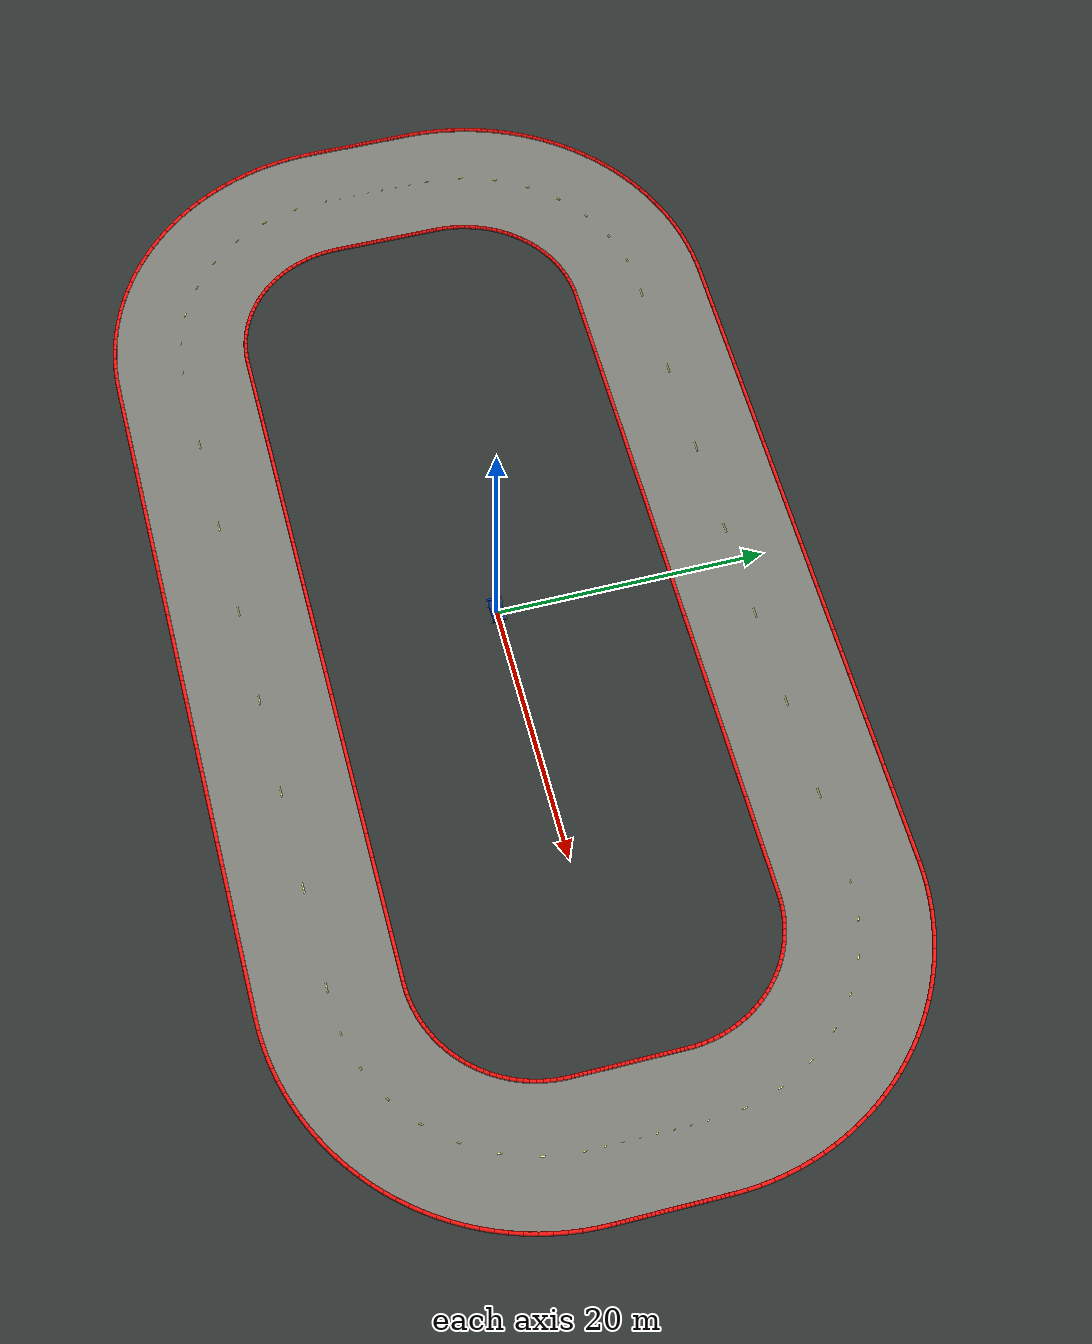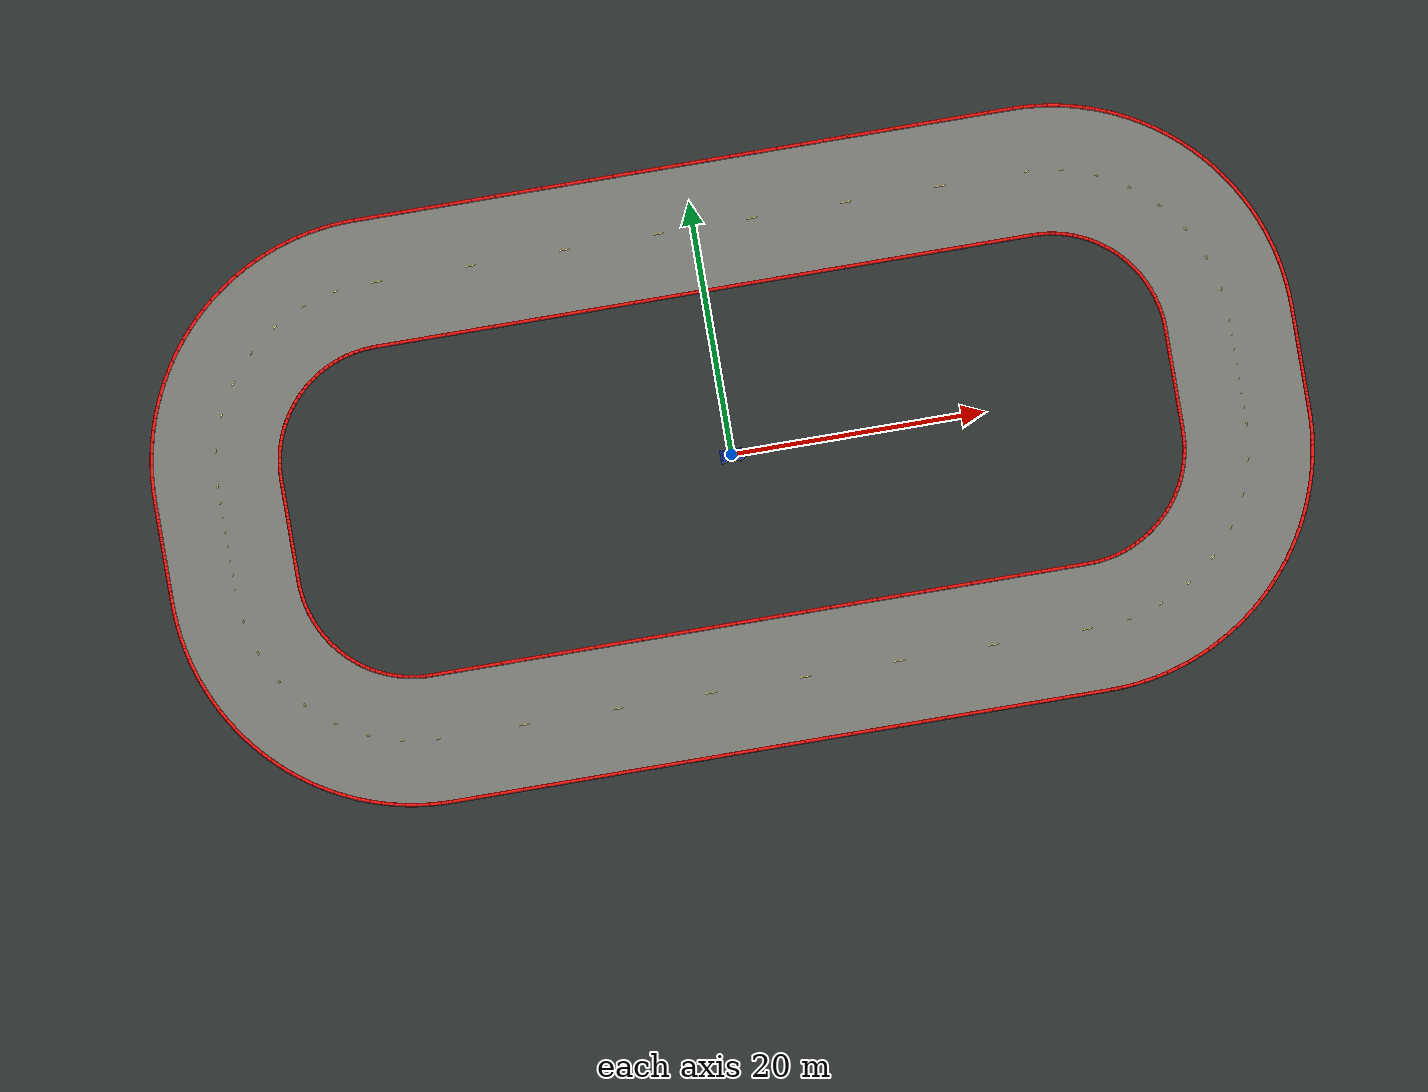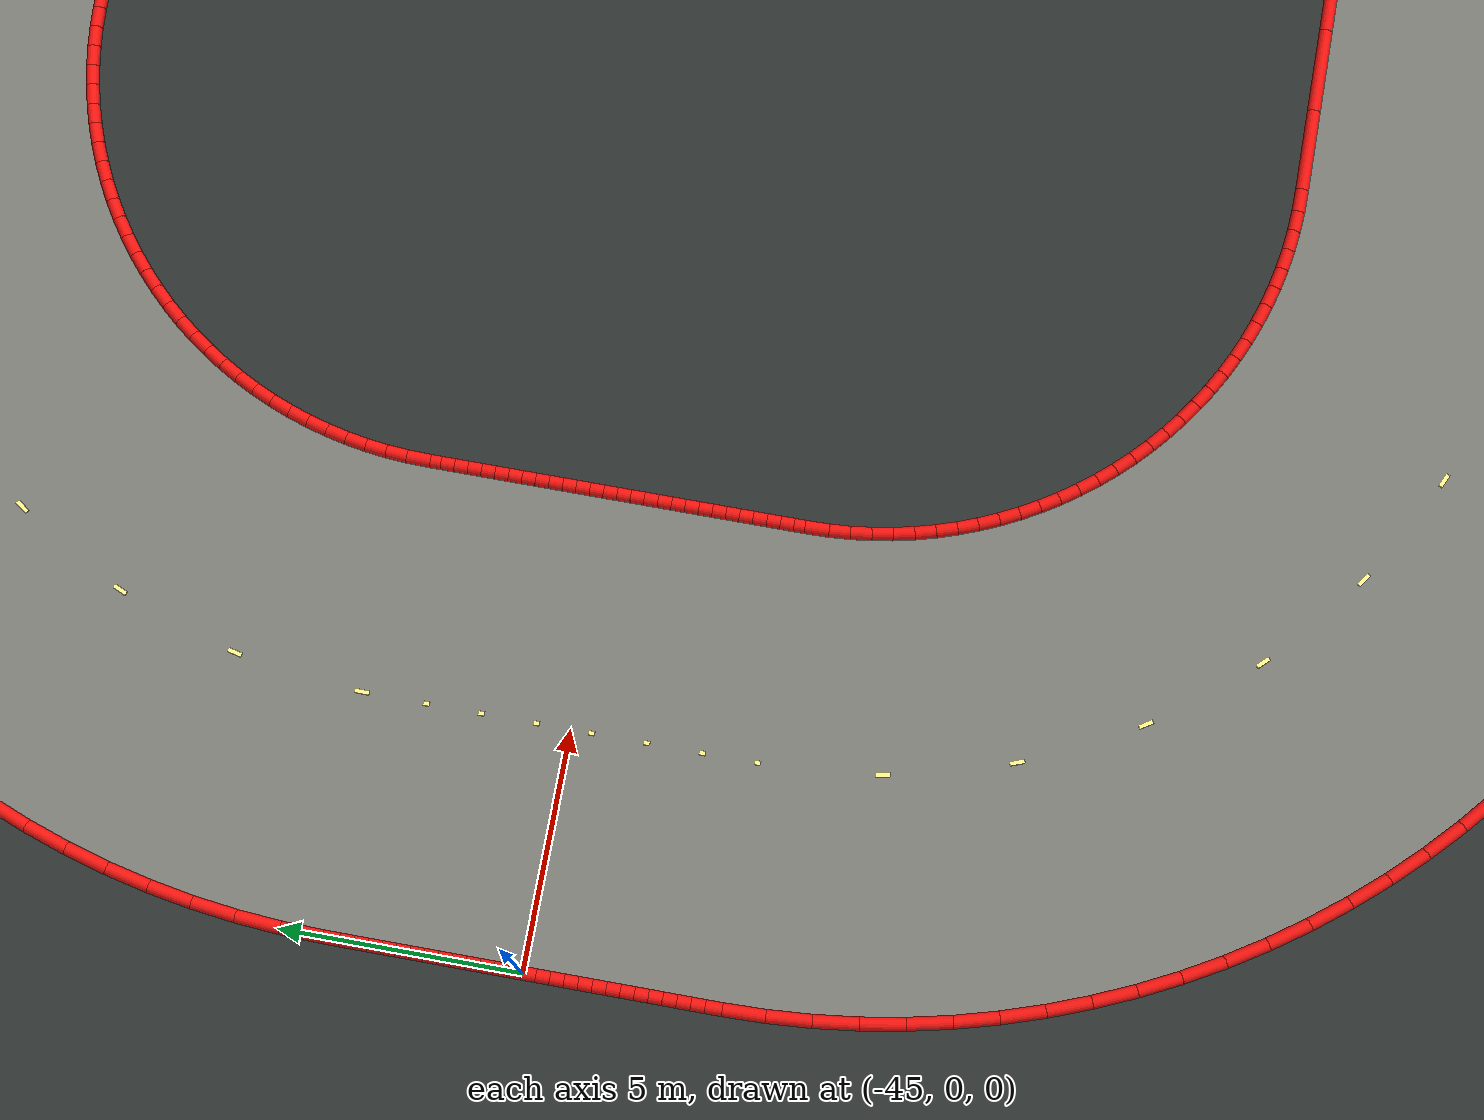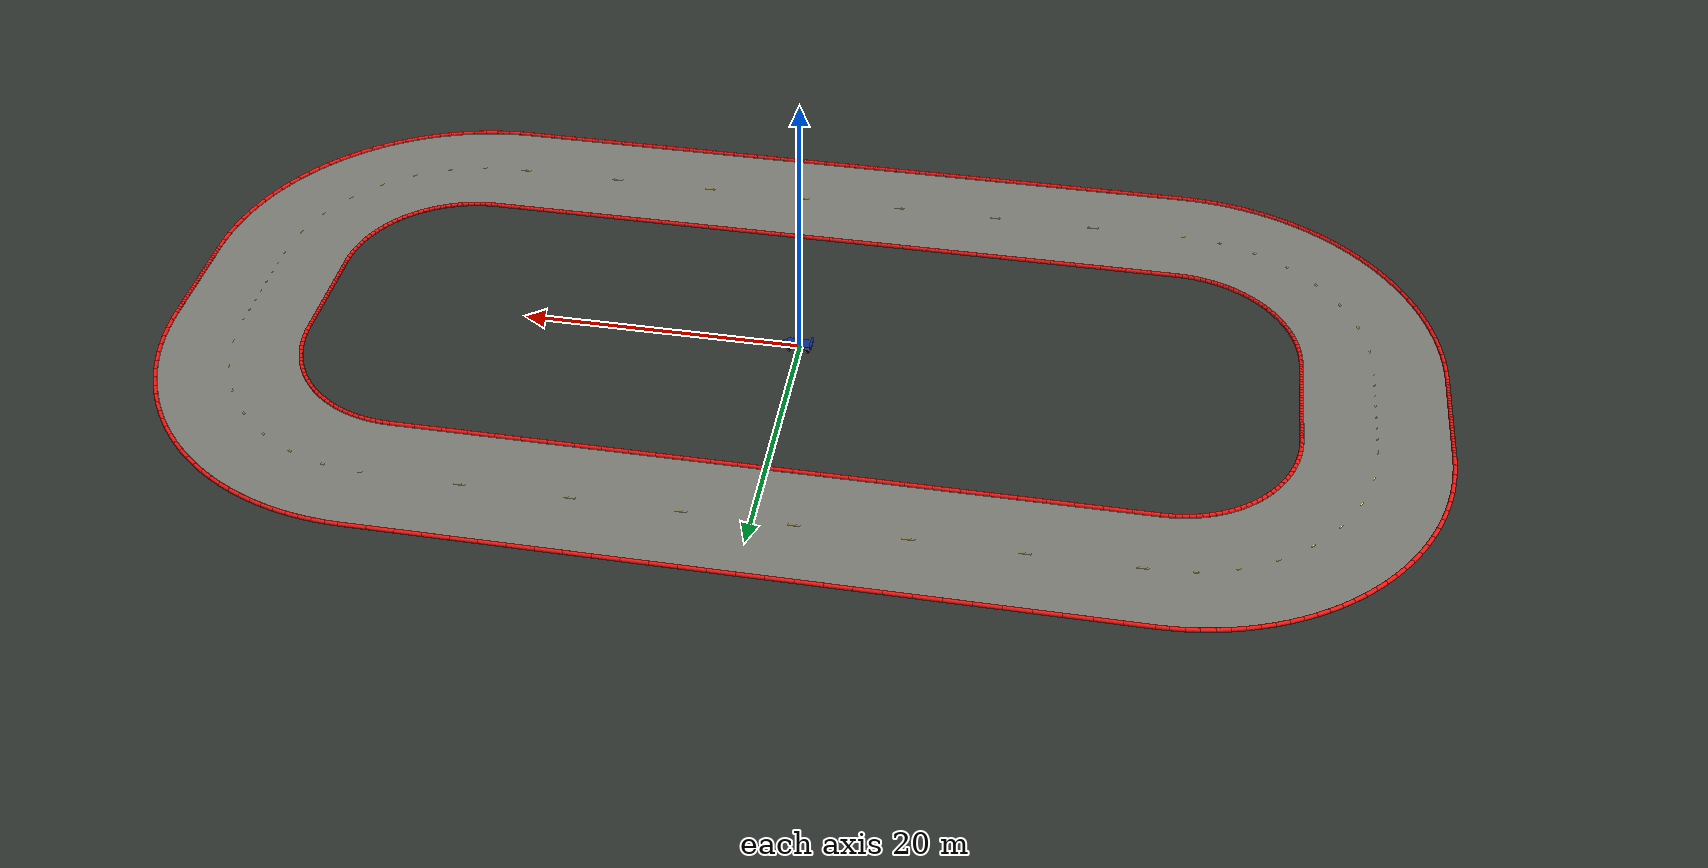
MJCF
<mujoco model="racesim_world">
  <compiler angle="degree" autolimits="true"/>
  <option timestep="0.02" gravity="0 0 -9.81"/>
  <visual>
    <global offwidth="1280" offheight="960"/>
    <headlight ambient="0.35 0.35 0.35" diffuse="0.8 0.8 0.8"/>
  </visual>

  <include file="car.xml"/>
  <include file="oval_track.xml"/>

  <asset>
    <texture name="grid" type="2d" builtin="checker" width="512" height="512"
             rgb1="0.16 0.18 0.17" rgb2="0.20 0.22 0.21"/>
    <material name="ground" texture="grid" texrepeat="12 12" reflectance="0.05"/>
  </asset>

  <worldbody>
    <light name="sun" pos="0 0 30" dir="0 0 -1" diffuse="1.0 1.0 1.0" ambient="0.25 0.25 0.25"/>
    <geom name="ground" type="plane" size="80 80 0.1" material="ground"/>
    <camera name="topdown" pos="0 0 120" xyaxes="1 0 0 0 1 0" fovy="42"/>
    <camera name="follow" mode="trackcom" target="car" pos="-5 0 3" xyaxes="0 -1 0 0.5 0 0.866"/>
  </worldbody>
</mujoco>

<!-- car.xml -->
<mujoco model="simple_car">
  <default>
    <geom friction="1.2 0.02 0.001" density="600"/>
    <joint damping="0.1"/>
  </default>

  <asset>
    <material name="chassis_blue" rgba="0.05 0.18 0.55 1"/>
    <material name="wheel_dark" rgba="0.02 0.02 0.025 1"/>
  </asset>

  <worldbody>
    <body name="car" pos="0 0 0.28">
      <freejoint name="root"/>
      <geom name="chassis" type="box" size="0.9 0.45 0.12" material="chassis_blue"/>
      <geom name="nose" type="box" pos="0.75 0 0.02" size="0.45 0.25 0.06" material="chassis_blue"/>
      <geom name="rear_wing" type="box" pos="-0.85 0 0.22" size="0.08 0.55 0.04" material="chassis_blue"/>

      <body name="front_left_wheel" pos="0.65 0.48 -0.12">
        <joint name="front_left_spin" type="hinge" axis="0 1 0"/>
        <geom type="cylinder" size="0.18 0.08" euler="90 0 0" material="wheel_dark"/>
      </body>
      <body name="front_right_wheel" pos="0.65 -0.48 -0.12">
        <joint name="front_right_spin" type="hinge" axis="0 1 0"/>
        <geom type="cylinder" size="0.18 0.08" euler="90 0 0" material="wheel_dark"/>
      </body>
      <body name="rear_left_wheel" pos="-0.65 0.48 -0.12">
        <joint name="rear_left_spin" type="hinge" axis="0 1 0"/>
        <geom type="cylinder" size="0.18 0.08" euler="90 0 0" material="wheel_dark"/>
      </body>
      <body name="rear_right_wheel" pos="-0.65 -0.48 -0.12">
        <joint name="rear_right_spin" type="hinge" axis="0 1 0"/>
        <geom type="cylinder" size="0.18 0.08" euler="90 0 0" material="wheel_dark"/>
      </body>
    </body>
  </worldbody>
</mujoco>

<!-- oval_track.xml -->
<mujoco model="oval_track_visuals">
  <asset>
    <mesh name="track_surface_mesh" vertex="44.99962 4.06136 0.02200 45.00000 3.71429 0.02200 45.00000 3.42857 0.02200 45.00000 3.14286 0.02200 45.00000 2.85714 0.02200 45.00000 2.57143 0.02200 45.00000 2.28571 0.02200 45.00000 2.00000 0.02200 45.00000 1.71429 0.02200 45.00000 1.42857 0.02200 45.00000 1.14286 0.02200 45.00000 0.85714 0.02200 45.00000 0.57143 0.02200 45.00000 0.28571 0.02200 45.00000 0.00000 0.02200 45.00000 -0.28571 0.02200 45.00000 -0.57143 0.02200 45.00000 -0.85714 0.02200 45.00000 -1.14286 0.02200 45.00000 -1.42857 0.02200 45.00000 -1.71429 0.02200 45.00000 -2.00000 0.02200 45.00000 -2.28571 0.02200 45.00000 -2.57143 0.02200 45.00000 -2.85714 0.02200 45.00000 -3.14286 0.02200 45.00000 -3.42857 0.02200 45.00000 -3.71429 0.02200 44.99962 -4.06136 0.02200 44.97711 -4.93229 0.02200 44.90851 -5.86233 0.02200 44.79435 -6.78788 0.02200 44.63492 -7.70672 0.02200 44.43059 -8.61662 0.02200 44.18187 -9.51541 0.02200 43.88934 -10.40091 0.02200 43.55371 -11.27099 0.02200 43.17580 -12.12355 0.02200 42.75650 -12.95654 0.02200 42.29684 -13.76795 0.02200 41.79792 -14.55583 0.02200 41.26094 -15.31829 0.02200 40.68720 -16.05347 0.02200 40.07807 -16.75962 0.02200 39.43503 -17.43503 0.02200 38.75962 -18.07807 0.02200 38.05347 -18.68720 0.02200 37.31829 -19.26094 0.02200 36.55583 -19.79792 0.02200 35.76795 -20.29684 0.02200 34.95654 -20.75650 0.02200 34.12355 -21.17580 0.02200 33.27099 -21.55371 0.02200 32.40091 -21.88934 0.02200 31.51541 -22.18187 0.02200 30.61662 -22.43059 0.02200 29.70672 -22.63492 0.02200 28.78788 -22.79435 0.02200 27.86233 -22.90851 0.02200 26.93229 -22.97711 0.02200 26.06136 -22.99962 0.02200 24.14286 -23.00000 0.02200 22.28571 -23.00000 0.02200 20.42857 -23.00000 0.02200 18.57143 -23.00000 0.02200 16.71429 -23.00000 0.02200 14.85714 -23.00000 0.02200 13.00000 -23.00000 0.02200 11.14286 -23.00000 0.02200 9.28571 -23.00000 0.02200 7.42857 -23.00000 0.02200 5.57143 -23.00000 0.02200 3.71429 -23.00000 0.02200 1.85714 -23.00000 0.02200 0.00000 -23.00000 0.02200 -1.85714 -23.00000 0.02200 -3.71429 -23.00000 0.02200 -5.57143 -23.00000 0.02200 -7.42857 -23.00000 0.02200 -9.28571 -23.00000 0.02200 -11.14286 -23.00000 0.02200 -13.00000 -23.00000 0.02200 -14.85714 -23.00000 0.02200 -16.71429 -23.00000 0.02200 -18.57143 -23.00000 0.02200 -20.42857 -23.00000 0.02200 -22.28571 -23.00000 0.02200 -24.14286 -23.00000 0.02200 -26.06136 -22.99962 0.02200 -26.93229 -22.97711 0.02200 -27.86233 -22.90851 0.02200 -28.78788 -22.79435 0.02200 -29.70672 -22.63492 0.02200 -30.61662 -22.43059 0.02200 -31.51541 -22.18187 0.02200 -32.40091 -21.88934 0.02200 -33.27099 -21.55371 0.02200 -34.12355 -21.17580 0.02200 -34.95654 -20.75650 0.02200 -35.76795 -20.29684 0.02200 -36.55583 -19.79792 0.02200 -37.31829 -19.26094 0.02200 -38.05347 -18.68720 0.02200 -38.75962 -18.07807 0.02200 -39.43503 -17.43503 0.02200 -40.07807 -16.75962 0.02200 -40.68720 -16.05347 0.02200 -41.26094 -15.31829 0.02200 -41.79792 -14.55583 0.02200 -42.29684 -13.76795 0.02200 -42.75650 -12.95654 0.02200 -43.17580 -12.12355 0.02200 -43.55371 -11.27099 0.02200 -43.88934 -10.40091 0.02200 -44.18187 -9.51541 0.02200 -44.43059 -8.61662 0.02200 -44.63492 -7.70672 0.02200 -44.79435 -6.78788 0.02200 -44.90851 -5.86233 0.02200 -44.97711 -4.93229 0.02200 -44.99962 -4.06136 0.02200 -45.00000 -3.71429 0.02200 -45.00000 -3.42857 0.02200 -45.00000 -3.14286 0.02200 -45.00000 -2.85714 0.02200 -45.00000 -2.57143 0.02200 -45.00000 -2.28571 0.02200 -45.00000 -2.00000 0.02200 -45.00000 -1.71429 0.02200 -45.00000 -1.42857 0.02200 -45.00000 -1.14286 0.02200 -45.00000 -0.85714 0.02200 -45.00000 -0.57143 0.02200 -45.00000 -0.28571 0.02200 -45.00000 -0.00000 0.02200 -45.00000 0.28571 0.02200 -45.00000 0.57143 0.02200 -45.00000 0.85714 0.02200 -45.00000 1.14286 0.02200 -45.00000 1.42857 0.02200 -45.00000 1.71429 0.02200 -45.00000 2.00000 0.02200 -45.00000 2.28571 0.02200 -45.00000 2.57143 0.02200 -45.00000 2.85714 0.02200 -45.00000 3.14286 0.02200 -45.00000 3.42857 0.02200 -45.00000 3.71429 0.02200 -44.99962 4.06136 0.02200 -44.97711 4.93229 0.02200 -44.90851 5.86233 0.02200 -44.79435 6.78788 0.02200 -44.63492 7.70672 0.02200 -44.43059 8.61662 0.02200 -44.18187 9.51541 0.02200 -43.88934 10.40091 0.02200 -43.55371 11.27099 0.02200 -43.17580 12.12355 0.02200 -42.75650 12.95654 0.02200 -42.29684 13.76795 0.02200 -41.79792 14.55583 0.02200 -41.26094 15.31829 0.02200 -40.68720 16.05347 0.02200 -40.07807 16.75962 0.02200 -39.43503 17.43503 0.02200 -38.75962 18.07807 0.02200 -38.05347 18.68720 0.02200 -37.31829 19.26094 0.02200 -36.55583 19.79792 0.02200 -35.76795 20.29684 0.02200 -34.95654 20.75650 0.02200 -34.12355 21.17580 0.02200 -33.27099 21.55371 0.02200 -32.40091 21.88934 0.02200 -31.51541 22.18187 0.02200 -30.61662 22.43059 0.02200 -29.70672 22.63492 0.02200 -28.78788 22.79435 0.02200 -27.86233 22.90851 0.02200 -26.93229 22.97711 0.02200 -26.06136 22.99962 0.02200 -24.14286 23.00000 0.02200 -22.28571 23.00000 0.02200 -20.42857 23.00000 0.02200 -18.57143 23.00000 0.02200 -16.71429 23.00000 0.02200 -14.85714 23.00000 0.02200 -13.00000 23.00000 0.02200 -11.14286 23.00000 0.02200 -9.28571 23.00000 0.02200 -7.42857 23.00000 0.02200 -5.57143 23.00000 0.02200 -3.71429 23.00000 0.02200 -1.85714 23.00000 0.02200 -0.00000 23.00000 0.02200 1.85714 23.00000 0.02200 3.71429 23.00000 0.02200 5.57143 23.00000 0.02200 7.42857 23.00000 0.02200 9.28571 23.00000 0.02200 11.14286 23.00000 0.02200 13.00000 23.00000 0.02200 14.85714 23.00000 0.02200 16.71429 23.00000 0.02200 18.57143 23.00000 0.02200 20.42857 23.00000 0.02200 22.28571 23.00000 0.02200 24.14286 23.00000 0.02200 26.06136 22.99962 0.02200 26.93229 22.97711 0.02200 27.86233 22.90851 0.02200 28.78788 22.79435 0.02200 29.70672 22.63492 0.02200 30.61662 22.43059 0.02200 31.51541 22.18187 0.02200 32.40091 21.88934 0.02200 33.27099 21.55371 0.02200 34.12355 21.17580 0.02200 34.95654 20.75650 0.02200 35.76795 20.29684 0.02200 36.55583 19.79792 0.02200 37.31829 19.26094 0.02200 38.05347 18.68720 0.02200 38.75962 18.07807 0.02200 39.43503 17.43503 0.02200 40.07807 16.75962 0.02200 40.68720 16.05347 0.02200 41.26094 15.31829 0.02200 41.79792 14.55583 0.02200 42.29684 13.76795 0.02200 42.75650 12.95654 0.02200 43.17580 12.12355 0.02200 43.55371 11.27099 0.02200 43.88934 10.40091 0.02200 44.18187 9.51541 0.02200 44.43059 8.61662 0.02200 44.63492 7.70672 0.02200 44.79435 6.78788 0.02200 44.90851 5.86233 0.02200 44.97711 4.93229 0.02200 35.00038 3.93864 0.02200 35.00000 3.71429 0.02200 35.00000 3.42857 0.02200 35.00000 3.14286 0.02200 35.00000 2.85714 0.02200 35.00000 2.57143 0.02200 35.00000 2.28571 0.02200 35.00000 2.00000 0.02200 35.00000 1.71429 0.02200 35.00000 1.42857 0.02200 35.00000 1.14286 0.02200 35.00000 0.85714 0.02200 35.00000 0.57143 0.02200 35.00000 0.28571 0.02200 35.00000 0.00000 0.02200 35.00000 -0.28571 0.02200 35.00000 -0.57143 0.02200 35.00000 -0.85714 0.02200 35.00000 -1.14286 0.02200 35.00000 -1.42857 0.02200 35.00000 -1.71429 0.02200 35.00000 -2.00000 0.02200 35.00000 -2.28571 0.02200 35.00000 -2.57143 0.02200 35.00000 -2.85714 0.02200 35.00000 -3.14286 0.02200 35.00000 -3.42857 0.02200 35.00000 -3.71429 0.02200 35.00038 -3.93864 0.02200 34.98916 -4.44161 0.02200 34.95666 -4.88215 0.02200 34.90259 -5.32057 0.02200 34.82707 -5.75581 0.02200 34.73028 -6.18682 0.02200 34.61246 -6.61256 0.02200 34.47390 -7.03201 0.02200 34.31492 -7.44415 0.02200 34.13590 -7.84800 0.02200 33.93729 -8.24257 0.02200 33.71956 -8.62692 0.02200 33.48323 -9.00013 0.02200 33.22887 -9.36129 0.02200 32.95709 -9.70954 0.02200 32.66856 -10.04403 0.02200 32.36396 -10.36396 0.02200 32.04403 -10.66856 0.02200 31.70954 -10.95709 0.02200 31.36129 -11.22887 0.02200 31.00013 -11.48323 0.02200 30.62692 -11.71956 0.02200 30.24257 -11.93729 0.02200 29.84800 -12.13590 0.02200 29.44415 -12.31492 0.02200 29.03201 -12.47390 0.02200 28.61256 -12.61246 0.02200 28.18682 -12.73028 0.02200 27.75581 -12.82707 0.02200 27.32057 -12.90259 0.02200 26.88215 -12.95666 0.02200 26.44161 -12.98916 0.02200 25.93864 -13.00038 0.02200 24.14286 -13.00000 0.02200 22.28571 -13.00000 0.02200 20.42857 -13.00000 0.02200 18.57143 -13.00000 0.02200 16.71429 -13.00000 0.02200 14.85714 -13.00000 0.02200 13.00000 -13.00000 0.02200 11.14286 -13.00000 0.02200 9.28571 -13.00000 0.02200 7.42857 -13.00000 0.02200 5.57143 -13.00000 0.02200 3.71429 -13.00000 0.02200 1.85714 -13.00000 0.02200 0.00000 -13.00000 0.02200 -1.85714 -13.00000 0.02200 -3.71429 -13.00000 0.02200 -5.57143 -13.00000 0.02200 -7.42857 -13.00000 0.02200 -9.28571 -13.00000 0.02200 -11.14286 -13.00000 0.02200 -13.00000 -13.00000 0.02200 -14.85714 -13.00000 0.02200 -16.71429 -13.00000 0.02200 -18.57143 -13.00000 0.02200 -20.42857 -13.00000 0.02200 -22.28571 -13.00000 0.02200 -24.14286 -13.00000 0.02200 -25.93864 -13.00038 0.02200 -26.44161 -12.98916 0.02200 -26.88215 -12.95666 0.02200 -27.32057 -12.90259 0.02200 -27.75581 -12.82707 0.02200 -28.18682 -12.73028 0.02200 -28.61256 -12.61246 0.02200 -29.03201 -12.47390 0.02200 -29.44415 -12.31492 0.02200 -29.84800 -12.13590 0.02200 -30.24257 -11.93729 0.02200 -30.62692 -11.71956 0.02200 -31.00013 -11.48323 0.02200 -31.36129 -11.22887 0.02200 -31.70954 -10.95709 0.02200 -32.04403 -10.66856 0.02200 -32.36396 -10.36396 0.02200 -32.66856 -10.04403 0.02200 -32.95709 -9.70954 0.02200 -33.22887 -9.36129 0.02200 -33.48323 -9.00013 0.02200 -33.71956 -8.62692 0.02200 -33.93729 -8.24257 0.02200 -34.13590 -7.84800 0.02200 -34.31492 -7.44415 0.02200 -34.47390 -7.03201 0.02200 -34.61246 -6.61256 0.02200 -34.73028 -6.18682 0.02200 -34.82707 -5.75581 0.02200 -34.90259 -5.32057 0.02200 -34.95666 -4.88215 0.02200 -34.98916 -4.44161 0.02200 -35.00038 -3.93864 0.02200 -35.00000 -3.71429 0.02200 -35.00000 -3.42857 0.02200 -35.00000 -3.14286 0.02200 -35.00000 -2.85714 0.02200 -35.00000 -2.57143 0.02200 -35.00000 -2.28571 0.02200 -35.00000 -2.00000 0.02200 -35.00000 -1.71429 0.02200 -35.00000 -1.42857 0.02200 -35.00000 -1.14286 0.02200 -35.00000 -0.85714 0.02200 -35.00000 -0.57143 0.02200 -35.00000 -0.28571 0.02200 -35.00000 -0.00000 0.02200 -35.00000 0.28571 0.02200 -35.00000 0.57143 0.02200 -35.00000 0.85714 0.02200 -35.00000 1.14286 0.02200 -35.00000 1.42857 0.02200 -35.00000 1.71429 0.02200 -35.00000 2.00000 0.02200 -35.00000 2.28571 0.02200 -35.00000 2.57143 0.02200 -35.00000 2.85714 0.02200 -35.00000 3.14286 0.02200 -35.00000 3.42857 0.02200 -35.00000 3.71429 0.02200 -35.00038 3.93864 0.02200 -34.98916 4.44161 0.02200 -34.95666 4.88215 0.02200 -34.90259 5.32057 0.02200 -34.82707 5.75581 0.02200 -34.73028 6.18682 0.02200 -34.61246 6.61256 0.02200 -34.47390 7.03201 0.02200 -34.31492 7.44415 0.02200 -34.13590 7.84800 0.02200 -33.93729 8.24257 0.02200 -33.71956 8.62692 0.02200 -33.48323 9.00013 0.02200 -33.22887 9.36129 0.02200 -32.95709 9.70954 0.02200 -32.66856 10.04403 0.02200 -32.36396 10.36396 0.02200 -32.04403 10.66856 0.02200 -31.70954 10.95709 0.02200 -31.36129 11.22887 0.02200 -31.00013 11.48323 0.02200 -30.62692 11.71956 0.02200 -30.24257 11.93729 0.02200 -29.84800 12.13590 0.02200 -29.44415 12.31492 0.02200 -29.03201 12.47390 0.02200 -28.61256 12.61246 0.02200 -28.18682 12.73028 0.02200 -27.75581 12.82707 0.02200 -27.32057 12.90259 0.02200 -26.88215 12.95666 0.02200 -26.44161 12.98916 0.02200 -25.93864 13.00038 0.02200 -24.14286 13.00000 0.02200 -22.28571 13.00000 0.02200 -20.42857 13.00000 0.02200 -18.57143 13.00000 0.02200 -16.71429 13.00000 0.02200 -14.85714 13.00000 0.02200 -13.00000 13.00000 0.02200 -11.14286 13.00000 0.02200 -9.28571 13.00000 0.02200 -7.42857 13.00000 0.02200 -5.57143 13.00000 0.02200 -3.71429 13.00000 0.02200 -1.85714 13.00000 0.02200 -0.00000 13.00000 0.02200 1.85714 13.00000 0.02200 3.71429 13.00000 0.02200 5.57143 13.00000 0.02200 7.42857 13.00000 0.02200 9.28571 13.00000 0.02200 11.14286 13.00000 0.02200 13.00000 13.00000 0.02200 14.85714 13.00000 0.02200 16.71429 13.00000 0.02200 18.57143 13.00000 0.02200 20.42857 13.00000 0.02200 22.28571 13.00000 0.02200 24.14286 13.00000 0.02200 25.93864 13.00038 0.02200 26.44161 12.98916 0.02200 26.88215 12.95666 0.02200 27.32057 12.90259 0.02200 27.75581 12.82707 0.02200 28.18682 12.73028 0.02200 28.61256 12.61246 0.02200 29.03201 12.47390 0.02200 29.44415 12.31492 0.02200 29.84800 12.13590 0.02200 30.24257 11.93729 0.02200 30.62692 11.71956 0.02200 31.00013 11.48323 0.02200 31.36129 11.22887 0.02200 31.70954 10.95709 0.02200 32.04403 10.66856 0.02200 32.36396 10.36396 0.02200 32.66856 10.04403 0.02200 32.95709 9.70954 0.02200 33.22887 9.36129 0.02200 33.48323 9.00013 0.02200 33.71956 8.62692 0.02200 33.93729 8.24257 0.02200 34.13590 7.84800 0.02200 34.31492 7.44415 0.02200 34.47390 7.03201 0.02200 34.61246 6.61256 0.02200 34.73028 6.18682 0.02200 34.82707 5.75581 0.02200 34.90259 5.32057 0.02200 34.95666 4.88215 0.02200 34.98916 4.44161 0.02200" face="0 241 1 0 240 241 1 242 2 1 241 242 2 243 3 2 242 243 3 244 4 3 243 244 4 245 5 4 244 245 5 246 6 5 245 246 6 247 7 6 246 247 7 248 8 7 247 248 8 249 9 8 248 249 9 250 10 9 249 250 10 251 11 10 250 251 11 252 12 11 251 252 12 253 13 12 252 253 13 254 14 13 253 254 14 255 15 14 254 255 15 256 16 15 255 256 16 257 17 16 256 257 17 258 18 17 257 258 18 259 19 18 258 259 19 260 20 19 259 260 20 261 21 20 260 261 21 262 22 21 261 262 22 263 23 22 262 263 23 264 24 23 263 264 24 265 25 24 264 265 25 266 26 25 265 266 26 267 27 26 266 267 27 268 28 27 267 268 28 269 29 28 268 269 29 270 30 29 269 270 30 271 31 30 270 271 31 272 32 31 271 272 32 273 33 32 272 273 33 274 34 33 273 274 34 275 35 34 274 275 35 276 36 35 275 276 36 277 37 36 276 277 37 278 38 37 277 278 38 279 39 38 278 279 39 280 40 39 279 280 40 281 41 40 280 281 41 282 42 41 281 282 42 283 43 42 282 283 43 284 44 43 283 284 44 285 45 44 284 285 45 286 46 45 285 286 46 287 47 46 286 287 47 288 48 47 287 288 48 289 49 48 288 289 49 290 50 49 289 290 50 291 51 50 290 291 51 292 52 51 291 292 52 293 53 52 292 293 53 294 54 53 293 294 54 295 55 54 294 295 55 296 56 55 295 296 56 297 57 56 296 297 57 298 58 57 297 298 58 299 59 58 298 299 59 300 60 59 299 300 60 301 61 60 300 301 61 302 62 61 301 302 62 303 63 62 302 303 63 304 64 63 303 304 64 305 65 64 304 305 65 306 66 65 305 306 66 307 67 66 306 307 67 308 68 67 307 308 68 309 69 68 308 309 69 310 70 69 309 310 70 311 71 70 310 311 71 312 72 71 311 312 72 313 73 72 312 313 73 314 74 73 313 314 74 315 75 74 314 315 75 316 76 75 315 316 76 317 77 76 316 317 77 318 78 77 317 318 78 319 79 78 318 319 79 320 80 79 319 320 80 321 81 80 320 321 81 322 82 81 321 322 82 323 83 82 322 323 83 324 84 83 323 324 84 325 85 84 324 325 85 326 86 85 325 326 86 327 87 86 326 327 87 328 88 87 327 328 88 329 89 88 328 329 89 330 90 89 329 330 90 331 91 90 330 331 91 332 92 91 331 332 92 333 93 92 332 333 93 334 94 93 333 334 94 335 95 94 334 335 95 336 96 95 335 336 96 337 97 96 336 337 97 338 98 97 337 338 98 339 99 98 338 339 99 340 100 99 339 340 100 341 101 100 340 341 101 342 102 101 341 342 102 343 103 102 342 343 103 344 104 103 343 344 104 345 105 104 344 345 105 346 106 105 345 346 106 347 107 106 346 347 107 348 108 107 347 348 108 349 109 108 348 349 109 350 110 109 349 350 110 351 111 110 350 351 111 352 112 111 351 352 112 353 113 112 352 353 113 354 114 113 353 354 114 355 115 114 354 355 115 356 116 115 355 356 116 357 117 116 356 357 117 358 118 117 357 358 118 359 119 118 358 359 119 360 120 119 359 360 120 361 121 120 360 361 121 362 122 121 361 362 122 363 123 122 362 363 123 364 124 123 363 364 124 365 125 124 364 365 125 366 126 125 365 366 126 367 127 126 366 367 127 368 128 127 367 368 128 369 129 128 368 369 129 370 130 129 369 370 130 371 131 130 370 371 131 372 132 131 371 372 132 373 133 132 372 373 133 374 134 133 373 374 134 375 135 134 374 375 135 376 136 135 375 376 136 377 137 136 376 377 137 378 138 137 377 378 138 379 139 138 378 379 139 380 140 139 379 380 140 381 141 140 380 381 141 382 142 141 381 382 142 383 143 142 382 383 143 384 144 143 383 384 144 385 145 144 384 385 145 386 146 145 385 386 146 387 147 146 386 387 147 388 148 147 387 388 148 389 149 148 388 389 149 390 150 149 389 390 150 391 151 150 390 391 151 392 152 151 391 392 152 393 153 152 392 393 153 394 154 153 393 394 154 395 155 154 394 395 155 396 156 155 395 396 156 397 157 156 396 397 157 398 158 157 397 398 158 399 159 158 398 399 159 400 160 159 399 400 160 401 161 160 400 401 161 402 162 161 401 402 162 403 163 162 402 403 163 404 164 163 403 404 164 405 165 164 404 405 165 406 166 165 405 406 166 407 167 166 406 407 167 408 168 167 407 408 168 409 169 168 408 409 169 410 170 169 409 410 170 411 171 170 410 411 171 412 172 171 411 412 172 413 173 172 412 413 173 414 174 173 413 414 174 415 175 174 414 415 175 416 176 175 415 416 176 417 177 176 416 417 177 418 178 177 417 418 178 419 179 178 418 419 179 420 180 179 419 420 180 421 181 180 420 421 181 422 182 181 421 422 182 423 183 182 422 423 183 424 184 183 423 424 184 425 185 184 424 425 185 426 186 185 425 426 186 427 187 186 426 427 187 428 188 187 427 428 188 429 189 188 428 429 189 430 190 189 429 430 190 431 191 190 430 431 191 432 192 191 431 432 192 433 193 192 432 433 193 434 194 193 433 434 194 435 195 194 434 435 195 436 196 195 435 436 196 437 197 196 436 437 197 438 198 197 437 438 198 439 199 198 438 439 199 440 200 199 439 440 200 441 201 200 440 441 201 442 202 201 441 442 202 443 203 202 442 443 203 444 204 203 443 444 204 445 205 204 444 445 205 446 206 205 445 446 206 447 207 206 446 447 207 448 208 207 447 448 208 449 209 208 448 449 209 450 210 209 449 450 210 451 211 210 450 451 211 452 212 211 451 452 212 453 213 212 452 453 213 454 214 213 453 454 214 455 215 214 454 455 215 456 216 215 455 456 216 457 217 216 456 457 217 458 218 217 457 458 218 459 219 218 458 459 219 460 220 219 459 460 220 461 221 220 460 461 221 462 222 221 461 462 222 463 223 222 462 463 223 464 224 223 463 464 224 465 225 224 464 465 225 466 226 225 465 466 226 467 227 226 466 467 227 468 228 227 467 468 228 469 229 228 468 469 229 470 230 229 469 470 230 471 231 230 470 471 231 472 232 231 471 472 232 473 233 232 472 473 233 474 234 233 473 474 234 475 235 234 474 475 235 476 236 235 475 476 236 477 237 236 476 477 237 478 238 237 477 478 238 479 239 238 478 479 239 240 0 239 479 240"/>
    <material name="track_asphalt" rgba="0.48 0.49 0.46 1" emission="0.08"/>
    <material name="track_boundary" rgba="0.95 0.08 0.06 1" emission="0.05"/>
    <material name="track_centerline" rgba="1.0 0.95 0.55 1" emission="0.15"/>
  </asset>
  <worldbody>
    <geom name="track_surface" type="mesh" mesh="track_surface_mesh" material="track_asphalt" contype="0" conaffinity="0"/>
    <geom name="track_left_boundary_000" type="capsule" fromto="44.99962 4.06136 0.09 45.00000 3.71429 0.09" size="0.14" material="track_boundary" contype="0" conaffinity="0"/>
    <geom name="track_left_boundary_001" type="capsule" fromto="45.00000 3.71429 0.09 45.00000 3.42857 0.09" size="0.14" material="track_boundary" contype="0" conaffinity="0"/>
    <geom name="track_left_boundary_002" type="capsule" fromto="45.00000 3.42857 0.09 45.00000 3.14286 0.09" size="0.14" material="track_boundary" contype="0" conaffinity="0"/>
    <geom name="track_left_boundary_003" type="capsule" fromto="45.00000 3.14286 0.09 45.00000 2.85714 0.09" size="0.14" material="track_boundary" contype="0" conaffinity="0"/>
    <geom name="track_left_boundary_004" type="capsule" fromto="45.00000 2.85714 0.09 45.00000 2.57143 0.09" size="0.14" material="track_boundary" contype="0" conaffinity="0"/>
    <geom name="track_left_boundary_005" type="capsule" fromto="45.00000 2.57143 0.09 45.00000 2.28571 0.09" size="0.14" material="track_boundary" contype="0" conaffinity="0"/>
    <geom name="track_left_boundary_006" type="capsule" fromto="45.00000 2.28571 0.09 45.00000 2.00000 0.09" size="0.14" material="track_boundary" contype="0" conaffinity="0"/>
    <geom name="track_left_boundary_007" type="capsule" fromto="45.00000 2.00000 0.09 45.00000 1.71429 0.09" size="0.14" material="track_boundary" contype="0" conaffinity="0"/>
    <geom name="track_left_boundary_008" type="capsule" fromto="45.00000 1.71429 0.09 45.00000 1.42857 0.09" size="0.14" material="track_boundary" contype="0" conaffinity="0"/>
    <geom name="track_left_boundary_009" type="capsule" fromto="45.00000 1.42857 0.09 45.00000 1.14286 0.09" size="0.14" material="track_boundary" contype="0" conaffinity="0"/>
    <geom name="track_left_boundary_010" type="capsule" fromto="45.00000 1.14286 0.09 45.00000 0.85714 0.09" size="0.14" material="track_boundary" contype="0" conaffinity="0"/>
    <geom name="track_left_boundary_011" type="capsule" fromto="45.00000 0.85714 0.09 45.00000 0.57143 0.09" size="0.14" material="track_boundary" contype="0" conaffinity="0"/>
    <geom name="track_left_boundary_012" type="capsule" fromto="45.00000 0.57143 0.09 45.00000 0.28571 0.09" size="0.14" material="track_boundary" contype="0" conaffinity="0"/>
    <geom name="track_left_boundary_013" type="capsule" fromto="45.00000 0.28571 0.09 45.00000 0.00000 0.09" size="0.14" material="track_boundary" contype="0" conaffinity="0"/>
    <geom name="track_left_boundary_014" type="capsule" fromto="45.00000 0.00000 0.09 45.00000 -0.28571 0.09" size="0.14" material="track_boundary" contype="0" conaffinity="0"/>
    <geom name="track_left_boundary_015" type="capsule" fromto="45.00000 -0.28571 0.09 45.00000 -0.57143 0.09" size="0.14" material="track_boundary" contype="0" conaffinity="0"/>
    <geom name="track_left_boundary_016" type="capsule" fromto="45.00000 -0.57143 0.09 45.00000 -0.85714 0.09" size="0.14" material="track_boundary" contype="0" conaffinity="0"/>
    <geom name="track_left_boundary_017" type="capsule" fromto="45.00000 -0.85714 0.09 45.00000 -1.14286 0.09" size="0.14" material="track_boundary" contype="0" conaffinity="0"/>
    <geom name="track_left_boundary_018" type="capsule" fromto="45.00000 -1.14286 0.09 45.00000 -1.42857 0.09" size="0.14" material="track_boundary" contype="0" conaffinity="0"/>
    <geom name="track_left_boundary_019" type="capsule" fromto="45.00000 -1.42857 0.09 45.00000 -1.71429 0.09" size="0.14" material="track_boundary" contype="0" conaffinity="0"/>
    <geom name="track_left_boundary_020" type="capsule" fromto="45.00000 -1.71429 0.09 45.00000 -2.00000 0.09" size="0.14" material="track_boundary" contype="0" conaffinity="0"/>
    <geom name="track_left_boundary_021" type="capsule" fromto="45.00000 -2.00000 0.09 45.00000 -2.28571 0.09" size="0.14" material="track_boundary" contype="0" conaffinity="0"/>
    <geom name="track_left_boundary_022" type="capsule" fromto="45.00000 -2.28571 0.09 45.00000 -2.57143 0.09" size="0.14" material="track_boundary" contype="0" conaffinity="0"/>
    <geom name="track_left_boundary_023" type="capsule" fromto="45.00000 -2.57143 0.09 45.00000 -2.85714 0.09" size="0.14" material="track_boundary" contype="0" conaffinity="0"/>
    <geom name="track_left_boundary_024" type="capsule" fromto="45.00000 -2.85714 0.09 45.00000 -3.14286 0.09" size="0.14" material="track_boundary" contype="0" conaffinity="0"/>
    <geom name="track_left_boundary_025" type="capsule" fromto="45.00000 -3.14286 0.09 45.00000 -3.42857 0.09" size="0.14" material="track_boundary" contype="0" conaffinity="0"/>
    <geom name="track_left_boundary_026" type="capsule" fromto="45.00000 -3.42857 0.09 45.00000 -3.71429 0.09" size="0.14" material="track_boundary" contype="0" conaffinity="0"/>
    <geom name="track_left_boundary_027" type="capsule" fromto="45.00000 -3.71429 0.09 44.99962 -4.06136 0.09" size="0.14" material="track_boundary" contype="0" conaffinity="0"/>
    <geom name="track_left_boundary_028" type="capsule" fromto="44.99962 -4.06136 0.09 44.97711 -4.93229 0.09" size="0.14" material="track_boundary" contype="0" conaffinity="0"/>
    <geom name="track_left_boundary_029" type="capsule" fromto="44.97711 -4.93229 0.09 44.90851 -5.86233 0.09" size="0.14" material="track_boundary" contype="0" conaffinity="0"/>
    <geom name="track_left_boundary_030" type="capsule" fromto="44.90851 -5.86233 0.09 44.79435 -6.78788 0.09" size="0.14" material="track_boundary" contype="0" conaffinity="0"/>
    <geom name="track_left_boundary_031" type="capsule" fromto="44.79435 -6.78788 0.09 44.63492 -7.70672 0.09" size="0.14" material="track_boundary" contype="0" conaffinity="0"/>
    <geom name="track_left_boundary_032" type="capsule" fromto="44.63492 -7.70672 0.09 44.43059 -8.61662 0.09" size="0.14" material="track_boundary" contype="0" conaffinity="0"/>
    <geom name="track_left_boundary_033" type="capsule" fromto="44.43059 -8.61662 0.09 44.18187 -9.51541 0.09" size="0.14" material="track_boundary" contype="0" conaffinity="0"/>
    <geom name="track_left_boundary_034" type="capsule" fromto="44.18187 -9.51541 0.09 43.88934 -10.40091 0.09" size="0.14" material="track_boundary" contype="0" conaffinity="0"/>
    <geom name="track_left_boundary_035" type="capsule" fromto="43.88934 -10.40091 0.09 43.55371 -11.27099 0.09" size="0.14" material="track_boundary" contype="0" conaffinity="0"/>
    <geom name="track_left_boundary_036" type="capsule" fromto="43.55371 -11.27099 0.09 43.17580 -12.12355 0.09" size="0.14" material="track_boundary" contype="0" conaffinity="0"/>
    <geom name="track_left_boundary_037" type="capsule" fromto="43.17580 -12.12355 0.09 42.75650 -12.95654 0.09" size="0.14" material="track_boundary" contype="0" conaffinity="0"/>
    <geom name="track_left_boundary_038" type="capsule" fromto="42.75650 -12.95654 0.09 42.29684 -13.76795 0.09" size="0.14" material="track_boundary" contype="0" conaffinity="0"/>
    <geom name="track_left_boundary_039" type="capsule" fromto="42.29684 -13.76795 0.09 41.79792 -14.55583 0.09" size="0.14" material="track_boundary" contype="0" conaffinity="0"/>
    <geom name="track_left_boundary_040" type="capsule" fromto="41.79792 -14.55583 0.09 41.26094 -15.31829 0.09" size="0.14" material="track_boundary" contype="0" conaffinity="0"/>
    <geom name="track_left_boundary_041" type="capsule" fromto="41.26094 -15.31829 0.09 40.68720 -16.05347 0.09" size="0.14" material="track_boundary" contype="0" conaffinity="0"/>
    <geom name="track_left_boundary_042" type="capsule" fromto="40.68720 -16.05347 0.09 40.07807 -16.75962 0.09" size="0.14" material="track_boundary" contype="0" conaffinity="0"/>
    <geom name="track_left_boundary_043" type="capsule" fromto="40.07807 -16.75962 0.09 39.43503 -17.43503 0.09" size="0.14" material="track_boundary" contype="0" conaffinity="0"/>
    <geom name="track_left_boundary_044" type="capsule" fromto="39.43503 -17.43503 0.09 38.75962 -18.07807 0.09" size="0.14" material="track_boundary" contype="0" conaffinity="0"/>
    <geom name="track_left_boundary_045" type="capsule" fromto="38.75962 -18.07807 0.09 38.05347 -18.68720 0.09" size="0.14" material="track_boundary" contype="0" conaffinity="0"/>
    <geom name="track_left_boundary_046" type="capsule" fromto="38.05347 -18.68720 0.09 37.31829 -19.26094 0.09" size="0.14" material="track_boundary" contype="0" conaffinity="0"/>
    <geom name="track_left_boundary_047" type="capsule" fromto="37.31829 -19.26094 0.09 36.55583 -19.79792 0.09" size="0.14" material="track_boundary" contype="0" conaffinity="0"/>
    <geom name="track_left_boundary_048" type="capsule" fromto="36.55583 -19.79792 0.09 35.76795 -20.29684 0.09" size="0.14" material="track_boundary" contype="0" conaffinity="0"/>
    <geom name="track_left_boundary_049" type="capsule" fromto="35.76795 -20.29684 0.09 34.95654 -20.75650 0.09" size="0.14" material="track_boundary" contype="0" conaffinity="0"/>
    <geom name="track_left_boundary_050" type="capsule" fromto="34.95654 -20.75650 0.09 34.12355 -21.17580 0.09" size="0.14" material="track_boundary" contype="0" conaffinity="0"/>
    <geom name="track_left_boundary_051" type="capsule" fromto="34.12355 -21.17580 0.09 33.27099 -21.55371 0.09" size="0.14" material="track_boundary" contype="0" conaffinity="0"/>
    <geom name="track_left_boundary_052" type="capsule" fromto="33.27099 -21.55371 0.09 32.40091 -21.88934 0.09" size="0.14" material="track_boundary" contype="0" conaffinity="0"/>
    <geom name="track_left_boundary_053" type="capsule" fromto="32.40091 -21.88934 0.09 31.51541 -22.18187 0.09" size="0.14" material="track_boundary" contype="0" conaffinity="0"/>
    <geom name="track_left_boundary_054" type="capsule" fromto="31.51541 -22.18187 0.09 30.61662 -22.43059 0.09" size="0.14" material="track_boundary" contype="0" conaffinity="0"/>
    <geom name="track_left_boundary_055" type="capsule" fromto="30.61662 -22.43059 0.09 29.70672 -22.63492 0.09" size="0.14" material="track_boundary" contype="0" conaffinity="0"/>
    <geom name="track_left_boundary_056" type="capsule" fromto="29.70672 -22.63492 0.09 28.78788 -22.79435 0.09" size="0.14" material="track_boundary" contype="0" conaffinity="0"/>
    <geom name="track_left_boundary_057" type="capsule" fromto="28.78788 -22.79435 0.09 27.86233 -22.90851 0.09" size="0.14" material="track_boundary" contype="0" conaffinity="0"/>
    <geom name="track_left_boundary_058" type="capsule" fromto="27.86233 -22.90851 0.09 26.93229 -22.97711 0.09" size="0.14" material="track_boundary" contype="0" conaffinity="0"/>
    <geom name="track_left_boundary_059" type="capsule" fromto="26.93229 -22.97711 0.09 26.06136 -22.99962 0.09" size="0.14" material="track_boundary" contype="0" conaffinity="0"/>
    <geom name="track_left_boundary_060" type="capsule" fromto="26.06136 -22.99962 0.09 24.14286 -23.00000 0.09" size="0.14" material="track_boundary" contype="0" conaffinity="0"/>
    <geom name="track_left_boundary_061" type="capsule" fromto="24.14286 -23.00000 0.09 22.28571 -23.00000 0.09" size="0.14" material="track_boundary" contype="0" conaffinity="0"/>
    <geom name="track_left_boundary_062" type="capsule" fromto="22.28571 -23.00000 0.09 20.42857 -23.00000 0.09" size="0.14" material="track_boundary" contype="0" conaffinity="0"/>
    <geom name="track_left_boundary_063" type="capsule" fromto="20.42857 -23.00000 0.09 18.57143 -23.00000 0.09" size="0.14" material="track_boundary" contype="0" conaffinity="0"/>
    <geom name="track_left_boundary_064" type="capsule" fromto="18.57143 -23.00000 0.09 16.71429 -23.00000 0.09" size="0.14" material="track_boundary" contype="0" conaffinity="0"/>
    <geom name="track_left_boundary_065" type="capsule" fromto="16.71429 -23.00000 0.09 14.85714 -23.00000 0.09" size="0.14" material="track_boundary" contype="0" conaffinity="0"/>
    <geom name="track_left_boundary_066" type="capsule" fromto="14.85714 -23.00000 0.09 13.00000 -23.00000 0.09" size="0.14" material="track_boundary" contype="0" conaffinity="0"/>
    <geom name="track_left_boundary_067" type="capsule" fromto="13.00000 -23.00000 0.09 11.14286 -23.00000 0.09" size="0.14" material="track_boundary" contype="0" conaffinity="0"/>
    <geom name="track_left_boundary_068" type="capsule" fromto="11.14286 -23.00000 0.09 9.28571 -23.00000 0.09" size="0.14" material="track_boundary" contype="0" conaffinity="0"/>
    <geom name="track_left_boundary_069" type="capsule" fromto="9.28571 -23.00000 0.09 7.42857 -23.00000 0.09" size="0.14" material="track_boundary" contype="0" conaffinity="0"/>
    <geom name="track_left_boundary_070" type="capsule" fromto="7.42857 -23.00000 0.09 5.57143 -23.00000 0.09" size="0.14" material="track_boundary" contype="0" conaffinity="0"/>
    <geom name="track_left_boundary_071" type="capsule" fromto="5.57143 -23.00000 0.09 3.71429 -23.00000 0.09" size="0.14" material="track_boundary" contype="0" conaffinity="0"/>
    <geom name="track_left_boundary_072" type="capsule" fromto="3.71429 -23.00000 0.09 1.85714 -23.00000 0.09" size="0.14" material="track_boundary" contype="0" conaffinity="0"/>
    <geom name="track_left_boundary_073" type="capsule" fromto="1.85714 -23.00000 0.09 0.00000 -23.00000 0.09" size="0.14" material="track_boundary" contype="0" conaffinity="0"/>
    <geom name="track_left_boundary_074" type="capsule" fromto="0.00000 -23.00000 0.09 -1.85714 -23.00000 0.09" size="0.14" material="track_boundary" contype="0" conaffinity="0"/>
    <geom name="track_left_boundary_075" type="capsule" fromto="-1.85714 -23.00000 0.09 -3.71429 -23.00000 0.09" size="0.14" material="track_boundary" contype="0" conaffinity="0"/>
    <geom name="track_left_boundary_076" type="capsule" fromto="-3.71429 -23.00000 0.09 -5.57143 -23.00000 0.09" size="0.14" material="track_boundary" contype="0" conaffinity="0"/>
    <geom name="track_left_boundary_077" type="capsule" fromto="-5.57143 -23.00000 0.09 -7.42857 -23.00000 0.09" size="0.14" material="track_boundary" contype="0" conaffinity="0"/>
    <geom name="track_left_boundary_078" type="capsule" fromto="-7.42857 -23.00000 0.09 -9.28571 -23.00000 0.09" size="0.14" material="track_boundary" contype="0" conaffinity="0"/>
    <geom name="track_left_boundary_079" type="capsule" fromto="-9.28571 -23.00000 0.09 -11.14286 -23.00000 0.09" size="0.14" material="track_boundary" contype="0" conaffinity="0"/>
    <geom name="track_left_boundary_080" type="capsule" fromto="-11.14286 -23.00000 0.09 -13.00000 -23.00000 0.09" size="0.14" material="track_boundary" contype="0" conaffinity="0"/>
    <geom name="track_left_boundary_081" type="capsule" fromto="-13.00000 -23.00000 0.09 -14.85714 -23.00000 0.09" size="0.14" material="track_boundary" contype="0" conaffinity="0"/>
    <geom name="track_left_boundary_082" type="capsule" fromto="-14.85714 -23.00000 0.09 -16.71429 -23.00000 0.09" size="0.14" material="track_boundary" contype="0" conaffinity="0"/>
    <geom name="track_left_boundary_083" type="capsule" fromto="-16.71429 -23.00000 0.09 -18.57143 -23.00000 0.09" size="0.14" material="track_boundary" contype="0" conaffinity="0"/>
    <geom name="track_left_boundary_084" type="capsule" fromto="-18.57143 -23.00000 0.09 -20.42857 -23.00000 0.09" size="0.14" material="track_boundary" contype="0" conaffinity="0"/>
    <geom name="track_left_boundary_085" type="capsule" fromto="-20.42857 -23.00000 0.09 -22.28571 -23.00000 0.09" size="0.14" material="track_boundary" contype="0" conaffinity="0"/>
    <geom name="track_left_boundary_086" type="capsule" fromto="-22.28571 -23.00000 0.09 -24.14286 -23.00000 0.09" size="0.14" material="track_boundary" contype="0" conaffinity="0"/>
    <geom name="track_left_boundary_087" type="capsule" fromto="-24.14286 -23.00000 0.09 -26.06136 -22.99962 0.09" size="0.14" material="track_boundary" contype="0" conaffinity="0"/>
    <geom name="track_left_boundary_088" type="capsule" fromto="-26.06136 -22.99962 0.09 -26.93229 -22.97711 0.09" size="0.14" material="track_boundary" contype="0" conaffinity="0"/>
    <geom name="track_left_boundary_089" type="capsule" fromto="-26.93229 -22.97711 0.09 -27.86233 -22.90851 0.09" size="0.14" material="track_boundary" contype="0" conaffinity="0"/>
    <geom name="track_left_boundary_090" type="capsule" fromto="-27.86233 -22.90851 0.09 -28.78788 -22.79435 0.09" size="0.14" material="track_boundary" contype="0" conaffinity="0"/>
    <geom name="track_left_boundary_091" type="capsule" fromto="-28.78788 -22.79435 0.09 -29.70672 -22.63492 0.09" size="0.14" material="track_boundary" contype="0" conaffinity="0"/>
    <geom name="track_left_boundary_092" type="capsule" fromto="-29.70672 -22.63492 0.09 -30.61662 -22.43059 0.09" size="0.14" material="track_boundary" contype="0" conaffinity="0"/>
    <geom name="track_left_boundary_093" type="capsule" fromto="-30.61662 -22.43059 0.09 -31.51541 -22.18187 0.09" size="0.14" material="track_boundary" contype="0" conaffinity="0"/>
    <geom name="track_left_boundary_094" type="capsule" fromto="-31.51541 -22.18187 0.09 -32.40091 -21.88934 0.09" size="0.14" material="track_boundary" contype="0" conaffinity="0"/>
    <geom name="track_left_boundary_095" type="capsule" fromto="-32.40091 -21.88934 0.09 -33.27099 -21.55371 0.09" size="0.14" material="track_boundary" contype="0" conaffinity="0"/>
    <geom name="track_left_boundary_096" type="capsule" fromto="-33.27099 -21.55371 0.09 -34.12355 -21.17580 0.09" size="0.14" material="track_boundary" contype="0" conaffinity="0"/>
    <geom name="track_left_boundary_097" type="capsule" fromto="-34.12355 -21.17580 0.09 -34.95654 -20.75650 0.09" size="0.14" material="track_boundary" contype="0" conaffinity="0"/>
    <geom name="track_left_boundary_098" type="capsule" fromto="-34.95654 -20.75650 0.09 -35.76795 -20.29684 0.09" size="0.14" material="track_boundary" contype="0" conaffinity="0"/>
    <geom name="track_left_boundary_099" type="capsule" fromto="-35.76795 -20.29684 0.09 -36.55583 -19.79792 0.09" size="0.14" material="track_boundary" contype="0" conaffinity="0"/>
    <geom name="track_left_boundary_100" type="capsule" fromto="-36.55583 -19.79792 0.09 -37.31829 -19.26094 0.09" size="0.14" material="track_boundary" contype="0" conaffinity="0"/>
    <geom name="track_left_boundary_101" type="capsule" fromto="-37.31829 -19.26094 0.09 -38.05347 -18.68720 0.09" size="0.14" material="track_boundary" contype="0" conaffinity="0"/>
    <geom name="track_left_boundary_102" type="capsule" fromto="-38.05347 -18.68720 0.09 -38.75962 -18.07807 0.09" size="0.14" material="track_boundary" contype="0" conaffinity="0"/>
    <geom name="track_left_boundary_103" type="capsule" fromto="-38.75962 -18.07807 0.09 -39.43503 -17.43503 0.09" size="0.14" material="track_boundary" contype="0" conaffinity="0"/>
    <geom name="track_left_boundary_104" type="capsule" fromto="-39.43503 -17.43503 0.09 -40.07807 -16.75962 0.09" size="0.14" material="track_boundary" contype="0" conaffinity="0"/>
    <geom name="track_left_boundary_105" type="capsule" fromto="-40.07807 -16.75962 0.09 -40.68720 -16.05347 0.09" size="0.14" material="track_boundary" contype="0" conaffinity="0"/>
    <geom name="track_left_boundary_106" type="capsule" fromto="-40.68720 -16.05347 0.09 -41.26094 -15.31829 0.09" size="0.14" material="track_boundary" contype="0" conaffinity="0"/>
    <geom name="track_left_boundary_107" type="capsule" fromto="-41.26094 -15.31829 0.09 -41.79792 -14.55583 0.09" size="0.14" material="track_boundary" contype="0" conaffinity="0"/>
    <geom name="track_left_boundary_108" type="capsule" fromto="-41.79792 -14.55583 0.09 -42.29684 -13.76795 0.09" size="0.14" material="track_boundary" contype="0" conaffinity="0"/>
    <geom name="track_left_boundary_109" type="capsule" fromto="-42.29684 -13.76795 0.09 -42.75650 -12.95654 0.09" size="0.14" material="track_boundary" contype="0" conaffinity="0"/>
    <geom name="track_left_boundary_110" type="capsule" fromto="-42.75650 -12.95654 0.09 -43.17580 -12.12355 0.09" size="0.14" material="track_boundary" contype="0" conaffinity="0"/>
    <geom name="track_left_boundary_111" type="capsule" fromto="-43.17580 -12.12355 0.09 -43.55371 -11.27099 0.09" size="0.14" material="track_boundary" contype="0" conaffinity="0"/>
    <geom name="track_left_boundary_112" type="capsule" fromto="-43.55371 -11.27099 0.09 -43.88934 -10.40091 0.09" size="0.14" material="track_boundary" contype="0" conaffinity="0"/>
    <geom name="track_left_boundary_113" type="capsule" fromto="-43.88934 -10.40091 0.09 -44.18187 -9.51541 0.09" size="0.14" material="track_boundary" contype="0" conaffinity="0"/>
    <geom name="track_left_boundary_114" type="capsule" fromto="-44.18187 -9.51541 0.09 -44.43059 -8.61662 0.09" size="0.14" material="track_boundary" contype="0" conaffinity="0"/>
    <geom name="track_left_boundary_115" type="capsule" fromto="-44.43059 -8.61662 0.09 -44.63492 -7.70672 0.09" size="0.14" material="track_boundary" contype="0" conaffinity="0"/>
    <geom name="track_left_boundary_116" type="capsule" fromto="-44.63492 -7.70672 0.09 -44.79435 -6.78788 0.09" size="0.14" material="track_boundary" contype="0" conaffinity="0"/>
    <geom name="track_left_boundary_117" type="capsule" fromto="-44.79435 -6.78788 0.09 -44.90851 -5.86233 0.09" size="0.14" material="track_boundary" contype="0" conaffinity="0"/>
    <geom name="track_left_boundary_118" type="capsule" fromto="-44.90851 -5.86233 0.09 -44.97711 -4.93229 0.09" size="0.14" material="track_boundary" contype="0" conaffinity="0"/>
    <geom name="track_left_boundary_119" type="capsule" fromto="-44.97711 -4.93229 0.09 -44.99962 -4.06136 0.09" size="0.14" material="track_boundary" contype="0" conaffinity="0"/>
    <geom name="track_left_boundary_120" type="capsule" fromto="-44.99962 -4.06136 0.09 -45.00000 -3.71429 0.09" size="0.14" material="track_boundary" contype="0" conaffinity="0"/>
    <geom name="track_left_boundary_121" type="capsule" fromto="-45.00000 -3.71429 0.09 -45.00000 -3.42857 0.09" size="0.14" material="track_boundary" contype="0" conaffinity="0"/>
    <geom name="track_left_boundary_122" type="capsule" fromto="-45.00000 -3.42857 0.09 -45.00000 -3.14286 0.09" size="0.14" material="track_boundary" contype="0" conaffinity="0"/>
    <geom name="track_left_boundary_123" type="capsule" fromto="-45.00000 -3.14286 0.09 -45.00000 -2.85714 0.09" size="0.14" material="track_boundary" contype="0" conaffinity="0"/>
    <geom name="track_left_boundary_124" type="capsule" fromto="-45.00000 -2.85714 0.09 -45.00000 -2.57143 0.09" size="0.14" material="track_boundary" contype="0" conaffinity="0"/>
    <geom name="track_left_boundary_125" type="capsule" fromto="-45.00000 -2.57143 0.09 -45.00000 -2.28571 0.09" size="0.14" material="track_boundary" contype="0" conaffinity="0"/>
    <geom name="track_left_boundary_126" type="capsule" fromto="-45.00000 -2.28571 0.09 -45.00000 -2.00000 0.09" size="0.14" material="track_boundary" contype="0" conaffinity="0"/>
    <geom name="track_left_boundary_127" type="capsule" fromto="-45.00000 -2.00000 0.09 -45.00000 -1.71429 0.09" size="0.14" material="track_boundary" contype="0" conaffinity="0"/>
    <geom name="track_left_boundary_128" type="capsule" fromto="-45.00000 -1.71429 0.09 -45.00000 -1.42857 0.09" size="0.14" material="track_boundary" contype="0" conaffinity="0"/>
    <geom name="track_left_boundary_129" type="capsule" fromto="-45.00000 -1.42857 0.09 -45.00000 -1.14286 0.09" size="0.14" material="track_boundary" contype="0" conaffinity="0"/>
    <geom name="track_left_boundary_130" type="capsule" fromto="-45.00000 -1.14286 0.09 -45.00000 -0.85714 0.09" size="0.14" material="track_boundary" contype="0" conaffinity="0"/>
    <geom name="track_left_boundary_131" type="capsule" fromto="-45.00000 -0.85714 0.09 -45.00000 -0.57143 0.09" size="0.14" material="track_boundary" contype="0" conaffinity="0"/>
    <geom name="track_left_boundary_132" type="capsule" fromto="-45.00000 -0.57143 0.09 -45.00000 -0.28571 0.09" size="0.14" material="track_boundary" contype="0" conaffinity="0"/>
    <geom name="track_left_boundary_133" type="capsule" fromto="-45.00000 -0.28571 0.09 -45.00000 -0.00000 0.09" size="0.14" material="track_boundary" contype="0" conaffinity="0"/>
    <geom name="track_left_boundary_134" type="capsule" fromto="-45.00000 -0.00000 0.09 -45.00000 0.28571 0.09" size="0.14" material="track_boundary" contype="0" conaffinity="0"/>
    <geom name="track_left_boundary_135" type="capsule" fromto="-45.00000 0.28571 0.09 -45.00000 0.57143 0.09" size="0.14" material="track_boundary" contype="0" conaffinity="0"/>
    <geom name="track_left_boundary_136" type="capsule" fromto="-45.00000 0.57143 0.09 -45.00000 0.85714 0.09" size="0.14" material="track_boundary" contype="0" conaffinity="0"/>
    <geom name="track_left_boundary_137" type="capsule" fromto="-45.00000 0.85714 0.09 -45.00000 1.14286 0.09" size="0.14" material="track_boundary" contype="0" conaffinity="0"/>
    <geom name="track_left_boundary_138" type="capsule" fromto="-45.00000 1.14286 0.09 -45.00000 1.42857 0.09" size="0.14" material="track_boundary" contype="0" conaffinity="0"/>
    <geom name="track_left_boundary_139" type="capsule" fromto="-45.00000 1.42857 0.09 -45.00000 1.71429 0.09" size="0.14" material="track_boundary" contype="0" conaffinity="0"/>
    <geom name="track_left_boundary_140" type="capsule" fromto="-45.00000 1.71429 0.09 -45.00000 2.00000 0.09" size="0.14" material="track_boundary" contype="0" conaffinity="0"/>
    <geom name="track_left_boundary_141" type="capsule" fromto="-45.00000 2.00000 0.09 -45.00000 2.28571 0.09" size="0.14" material="track_boundary" contype="0" conaffinity="0"/>
    <geom name="track_left_boundary_142" type="capsule" fromto="-45.00000 2.28571 0.09 -45.00000 2.57143 0.09" size="0.14" material="track_boundary" contype="0" conaffinity="0"/>
    <geom name="track_left_boundary_143" type="capsule" fromto="-45.00000 2.57143 0.09 -45.00000 2.85714 0.09" size="0.14" material="track_boundary" contype="0" conaffinity="0"/>
    <geom name="track_left_boundary_144" type="capsule" fromto="-45.00000 2.85714 0.09 -45.00000 3.14286 0.09" size="0.14" material="track_boundary" contype="0" conaffinity="0"/>
    <geom name="track_left_boundary_145" type="capsule" fromto="-45.00000 3.14286 0.09 -45.00000 3.42857 0.09" size="0.14" material="track_boundary" contype="0" conaffinity="0"/>
    <geom name="track_left_boundary_146" type="capsule" fromto="-45.00000 3.42857 0.09 -45.00000 3.71429 0.09" size="0.14" material="track_boundary" contype="0" conaffinity="0"/>
    <geom name="track_left_boundary_147" type="capsule" fromto="-45.00000 3.71429 0.09 -44.99962 4.06136 0.09" size="0.14" material="track_boundary" contype="0" conaffinity="0"/>
    <geom name="track_left_boundary_148" type="capsule" fromto="-44.99962 4.06136 0.09 -44.97711 4.93229 0.09" size="0.14" material="track_boundary" contype="0" conaffinity="0"/>
    <geom name="track_left_boundary_149" type="capsule" fromto="-44.97711 4.93229 0.09 -44.90851 5.86233 0.09" size="0.14" material="track_boundary" contype="0" conaffinity="0"/>
    <geom name="track_left_boundary_150" type="capsule" fromto="-44.90851 5.86233 0.09 -44.79435 6.78788 0.09" size="0.14" material="track_boundary" contype="0" conaffinity="0"/>
    <geom name="track_left_boundary_151" type="capsule" fromto="-44.79435 6.78788 0.09 -44.63492 7.70672 0.09" size="0.14" material="track_boundary" contype="0" conaffinity="0"/>
    <geom name="track_left_boundary_152" type="capsule" fromto="-44.63492 7.70672 0.09 -44.43059 8.61662 0.09" size="0.14" material="track_boundary" contype="0" conaffinity="0"/>
    <geom name="track_left_boundary_153" type="capsule" fromto="-44.43059 8.61662 0.09 -44.18187 9.51541 0.09" size="0.14" material="track_boundary" contype="0" conaffinity="0"/>
    <geom name="track_left_boundary_154" type="capsule" fromto="-44.18187 9.51541 0.09 -43.88934 10.40091 0.09" size="0.14" material="track_boundary" contype="0" conaffinity="0"/>
    <geom name="track_left_boundary_155" type="capsule" fromto="-43.88934 10.40091 0.09 -43.55371 11.27099 0.09" size="0.14" material="track_boundary" contype="0" conaffinity="0"/>
    <geom name="track_left_boundary_156" type="capsule" fromto="-43.55371 11.27099 0.09 -43.17580 12.12355 0.09" size="0.14" material="track_boundary" contype="0" conaffinity="0"/>
    <geom name="track_left_boundary_157" type="capsule" fromto="-43.17580 12.12355 0.09 -42.75650 12.95654 0.09" size="0.14" material="track_boundary" contype="0" conaffinity="0"/>
    <geom name="track_left_boundary_158" type="capsule" fromto="-42.75650 12.95654 0.09 -42.29684 13.76795 0.09" size="0.14" material="track_boundary" contype="0" conaffinity="0"/>
    <geom name="track_left_boundary_159" type="capsule" fromto="-42.29684 13.76795 0.09 -41.79792 14.55583 0.09" size="0.14" material="track_boundary" contype="0" conaffinity="0"/>
    <geom name="track_left_boundary_160" type="capsule" fromto="-41.79792 14.55583 0.09 -41.26094 15.31829 0.09" size="0.14" material="track_boundary" contype="0" conaffinity="0"/>
    <geom name="track_left_boundary_161" type="capsule" fromto="-41.26094 15.31829 0.09 -40.68720 16.05347 0.09" size="0.14" material="track_boundary" contype="0" conaffinity="0"/>
    <geom name="track_left_boundary_162" type="capsule" fromto="-40.68720 16.05347 0.09 -40.07807 16.75962 0.09" size="0.14" material="track_boundary" contype="0" conaffinity="0"/>
    <geom name="track_left_boundary_163" type="capsule" fromto="-40.07807 16.75962 0.09 -39.43503 17.43503 0.09" size="0.14" material="track_boundary" contype="0" conaffinity="0"/>
    <geom name="track_left_boundary_164" type="capsule" fromto="-39.43503 17.43503 0.09 -38.75962 18.07807 0.09" size="0.14" material="track_boundary" contype="0" conaffinity="0"/>
    <geom name="track_left_boundary_165" type="capsule" fromto="-38.75962 18.07807 0.09 -38.05347 18.68720 0.09" size="0.14" material="track_boundary" contype="0" conaffinity="0"/>
    <geom name="track_left_boundary_166" type="capsule" fromto="-38.05347 18.68720 0.09 -37.31829 19.26094 0.09" size="0.14" material="track_boundary" contype="0" conaffinity="0"/>
    <geom name="track_left_boundary_167" type="capsule" fromto="-37.31829 19.26094 0.09 -36.55583 19.79792 0.09" size="0.14" material="track_boundary" contype="0" conaffinity="0"/>
    <geom name="track_left_boundary_168" type="capsule" fromto="-36.55583 19.79792 0.09 -35.76795 20.29684 0.09" size="0.14" material="track_boundary" contype="0" conaffinity="0"/>
    <geom name="track_left_boundary_169" type="capsule" fromto="-35.76795 20.29684 0.09 -34.95654 20.75650 0.09" size="0.14" material="track_boundary" contype="0" conaffinity="0"/>
    <geom name="track_left_boundary_170" type="capsule" fromto="-34.95654 20.75650 0.09 -34.12355 21.17580 0.09" size="0.14" material="track_boundary" contype="0" conaffinity="0"/>
    <geom name="track_left_boundary_171" type="capsule" fromto="-34.12355 21.17580 0.09 -33.27099 21.55371 0.09" size="0.14" material="track_boundary" contype="0" conaffinity="0"/>
    <geom name="track_left_boundary_172" type="capsule" fromto="-33.27099 21.55371 0.09 -32.40091 21.88934 0.09" size="0.14" material="track_boundary" contype="0" conaffinity="0"/>
    <geom name="track_left_boundary_173" type="capsule" fromto="-32.40091 21.88934 0.09 -31.51541 22.18187 0.09" size="0.14" material="track_boundary" contype="0" conaffinity="0"/>
    <geom name="track_left_boundary_174" type="capsule" fromto="-31.51541 22.18187 0.09 -30.61662 22.43059 0.09" size="0.14" material="track_boundary" contype="0" conaffinity="0"/>
    <geom name="track_left_boundary_175" type="capsule" fromto="-30.61662 22.43059 0.09 -29.70672 22.63492 0.09" size="0.14" material="track_boundary" contype="0" conaffinity="0"/>
    <geom name="track_left_boundary_176" type="capsule" fromto="-29.70672 22.63492 0.09 -28.78788 22.79435 0.09" size="0.14" material="track_boundary" contype="0" conaffinity="0"/>
    <geom name="track_left_boundary_177" type="capsule" fromto="-28.78788 22.79435 0.09 -27.86233 22.90851 0.09" size="0.14" material="track_boundary" contype="0" conaffinity="0"/>
    <geom name="track_left_boundary_178" type="capsule" fromto="-27.86233 22.90851 0.09 -26.93229 22.97711 0.09" size="0.14" material="track_boundary" contype="0" conaffinity="0"/>
    <geom name="track_left_boundary_179" type="capsule" fromto="-26.93229 22.97711 0.09 -26.06136 22.99962 0.09" size="0.14" material="track_boundary" contype="0" conaffinity="0"/>
    <geom name="track_left_boundary_180" type="capsule" fromto="-26.06136 22.99962 0.09 -24.14286 23.00000 0.09" size="0.14" material="track_boundary" contype="0" conaffinity="0"/>
    <geom name="track_left_boundary_181" type="capsule" fromto="-24.14286 23.00000 0.09 -22.28571 23.00000 0.09" size="0.14" material="track_boundary" contype="0" conaffinity="0"/>
    <geom name="track_left_boundary_182" type="capsule" fromto="-22.28571 23.00000 0.09 -20.42857 23.00000 0.09" size="0.14" material="track_boundary" contype="0" conaffinity="0"/>
    <geom name="track_left_boundary_183" type="capsule" fromto="-20.42857 23.00000 0.09 -18.57143 23.00000 0.09" size="0.14" material="track_boundary" contype="0" conaffinity="0"/>
    <geom name="track_left_boundary_184" type="capsule" fromto="-18.57143 23.00000 0.09 -16.71429 23.00000 0.09" size="0.14" material="track_boundary" contype="0" conaffinity="0"/>
    <geom name="track_left_boundary_185" type="capsule" fromto="-16.71429 23.00000 0.09 -14.85714 23.00000 0.09" size="0.14" material="track_boundary" contype="0" conaffinity="0"/>
    <geom name="track_left_boundary_186" type="capsule" fromto="-14.85714 23.00000 0.09 -13.00000 23.00000 0.09" size="0.14" material="track_boundary" contype="0" conaffinity="0"/>
    <geom name="track_left_boundary_187" type="capsule" fromto="-13.00000 23.00000 0.09 -11.14286 23.00000 0.09" size="0.14" material="track_boundary" contype="0" conaffinity="0"/>
    <geom name="track_left_boundary_188" type="capsule" fromto="-11.14286 23.00000 0.09 -9.28571 23.00000 0.09" size="0.14" material="track_boundary" contype="0" conaffinity="0"/>
    <geom name="track_left_boundary_189" type="capsule" fromto="-9.28571 23.00000 0.09 -7.42857 23.00000 0.09" size="0.14" material="track_boundary" contype="0" conaffinity="0"/>
    <geom name="track_left_boundary_190" type="capsule" fromto="-7.42857 23.00000 0.09 -5.57143 23.00000 0.09" size="0.14" material="track_boundary" contype="0" conaffinity="0"/>
    <geom name="track_left_boundary_191" type="capsule" fromto="-5.57143 23.00000 0.09 -3.71429 23.00000 0.09" size="0.14" material="track_boundary" contype="0" conaffinity="0"/>
    <geom name="track_left_boundary_192" type="capsule" fromto="-3.71429 23.00000 0.09 -1.85714 23.00000 0.09" size="0.14" material="track_boundary" contype="0" conaffinity="0"/>
    <geom name="track_left_boundary_193" type="capsule" fromto="-1.85714 23.00000 0.09 -0.00000 23.00000 0.09" size="0.14" material="track_boundary" contype="0" conaffinity="0"/>
    <geom name="track_left_boundary_194" type="capsule" fromto="-0.00000 23.00000 0.09 1.85714 23.00000 0.09" size="0.14" material="track_boundary" contype="0" conaffinity="0"/>
    <geom name="track_left_boundary_195" type="capsule" fromto="1.85714 23.00000 0.09 3.71429 23.00000 0.09" size="0.14" material="track_boundary" contype="0" conaffinity="0"/>
    <geom name="track_left_boundary_196" type="capsule" fromto="3.71429 23.00000 0.09 5.57143 23.00000 0.09" size="0.14" material="track_boundary" contype="0" conaffinity="0"/>
    <geom name="track_left_boundary_197" type="capsule" fromto="5.57143 23.00000 0.09 7.42857 23.00000 0.09" size="0.14" material="track_boundary" contype="0" conaffinity="0"/>
    <geom name="track_left_boundary_198" type="capsule" fromto="7.42857 23.00000 0.09 9.28571 23.00000 0.09" size="0.14" material="track_boundary" contype="0" conaffinity="0"/>
    <geom name="track_left_boundary_199" type="capsule" fromto="9.28571 23.00000 0.09 11.14286 23.00000 0.09" size="0.14" material="track_boundary" contype="0" conaffinity="0"/>
    <geom name="track_left_boundary_200" type="capsule" fromto="11.14286 23.00000 0.09 13.00000 23.00000 0.09" size="0.14" material="track_boundary" contype="0" conaffinity="0"/>
    <geom name="track_left_boundary_201" type="capsule" fromto="13.00000 23.00000 0.09 14.85714 23.00000 0.09" size="0.14" material="track_boundary" contype="0" conaffinity="0"/>
    <geom name="track_left_boundary_202" type="capsule" fromto="14.85714 23.00000 0.09 16.71429 23.00000 0.09" size="0.14" material="track_boundary" contype="0" conaffinity="0"/>
    <geom name="track_left_boundary_203" type="capsule" fromto="16.71429 23.00000 0.09 18.57143 23.00000 0.09" size="0.14" material="track_boundary" contype="0" conaffinity="0"/>
    <geom name="track_left_boundary_204" type="capsule" fromto="18.57143 23.00000 0.09 20.42857 23.00000 0.09" size="0.14" material="track_boundary" contype="0" conaffinity="0"/>
    <geom name="track_left_boundary_205" type="capsule" fromto="20.42857 23.00000 0.09 22.28571 23.00000 0.09" size="0.14" material="track_boundary" contype="0" conaffinity="0"/>
    <geom name="track_left_boundary_206" type="capsule" fromto="22.28571 23.00000 0.09 24.14286 23.00000 0.09" size="0.14" material="track_boundary" contype="0" conaffinity="0"/>
    <geom name="track_left_boundary_207" type="capsule" fromto="24.14286 23.00000 0.09 26.06136 22.99962 0.09" size="0.14" material="track_boundary" contype="0" conaffinity="0"/>
    <geom name="track_left_boundary_208" type="capsule" fromto="26.06136 22.99962 0.09 26.93229 22.97711 0.09" size="0.14" material="track_boundary" contype="0" conaffinity="0"/>
    <geom name="track_left_boundary_209" type="capsule" fromto="26.93229 22.97711 0.09 27.86233 22.90851 0.09" size="0.14" material="track_boundary" contype="0" conaffinity="0"/>
    <geom name="track_left_boundary_210" type="capsule" fromto="27.86233 22.90851 0.09 28.78788 22.79435 0.09" size="0.14" material="track_boundary" contype="0" conaffinity="0"/>
    <geom name="track_left_boundary_211" type="capsule" fromto="28.78788 22.79435 0.09 29.70672 22.63492 0.09" size="0.14" material="track_boundary" contype="0" conaffinity="0"/>
    <geom name="track_left_boundary_212" type="capsule" fromto="29.70672 22.63492 0.09 30.61662 22.43059 0.09" size="0.14" material="track_boundary" contype="0" conaffinity="0"/>
    <geom name="track_left_boundary_213" type="capsule" fromto="30.61662 22.43059 0.09 31.51541 22.18187 0.09" size="0.14" material="track_boundary" contype="0" conaffinity="0"/>
    <geom name="track_left_boundary_214" type="capsule" fromto="31.51541 22.18187 0.09 32.40091 21.88934 0.09" size="0.14" material="track_boundary" contype="0" conaffinity="0"/>
    <geom name="track_left_boundary_215" type="capsule" fromto="32.40091 21.88934 0.09 33.27099 21.55371 0.09" size="0.14" material="track_boundary" contype="0" conaffinity="0"/>
    <geom name="track_left_boundary_216" type="capsule" fromto="33.27099 21.55371 0.09 34.12355 21.17580 0.09" size="0.14" material="track_boundary" contype="0" conaffinity="0"/>
    <geom name="track_left_boundary_217" type="capsule" fromto="34.12355 21.17580 0.09 34.95654 20.75650 0.09" size="0.14" material="track_boundary" contype="0" conaffinity="0"/>
    <geom name="track_left_boundary_218" type="capsule" fromto="34.95654 20.75650 0.09 35.76795 20.29684 0.09" size="0.14" material="track_boundary" contype="0" conaffinity="0"/>
    <geom name="track_left_boundary_219" type="capsule" fromto="35.76795 20.29684 0.09 36.55583 19.79792 0.09" size="0.14" material="track_boundary" contype="0" conaffinity="0"/>
    <geom name="track_left_boundary_220" type="capsule" fromto="36.55583 19.79792 0.09 37.31829 19.26094 0.09" size="0.14" material="track_boundary" contype="0" conaffinity="0"/>
    <geom name="track_left_boundary_221" type="capsule" fromto="37.31829 19.26094 0.09 38.05347 18.68720 0.09" size="0.14" material="track_boundary" contype="0" conaffinity="0"/>
    <geom name="track_left_boundary_222" type="capsule" fromto="38.05347 18.68720 0.09 38.75962 18.07807 0.09" size="0.14" material="track_boundary" contype="0" conaffinity="0"/>
    <geom name="track_left_boundary_223" type="capsule" fromto="38.75962 18.07807 0.09 39.43503 17.43503 0.09" size="0.14" material="track_boundary" contype="0" conaffinity="0"/>
    <geom name="track_left_boundary_224" type="capsule" fromto="39.43503 17.43503 0.09 40.07807 16.75962 0.09" size="0.14" material="track_boundary" contype="0" conaffinity="0"/>
    <geom name="track_left_boundary_225" type="capsule" fromto="40.07807 16.75962 0.09 40.68720 16.05347 0.09" size="0.14" material="track_boundary" contype="0" conaffinity="0"/>
    <geom name="track_left_boundary_226" type="capsule" fromto="40.68720 16.05347 0.09 41.26094 15.31829 0.09" size="0.14" material="track_boundary" contype="0" conaffinity="0"/>
    <geom name="track_left_boundary_227" type="capsule" fromto="41.26094 15.31829 0.09 41.79792 14.55583 0.09" size="0.14" material="track_boundary" contype="0" conaffinity="0"/>
    <geom name="track_left_boundary_228" type="capsule" fromto="41.79792 14.55583 0.09 42.29684 13.76795 0.09" size="0.14" material="track_boundary" contype="0" conaffinity="0"/>
    <geom name="track_left_boundary_229" type="capsule" fromto="42.29684 13.76795 0.09 42.75650 12.95654 0.09" size="0.14" material="track_boundary" contype="0" conaffinity="0"/>
    <geom name="track_left_boundary_230" type="capsule" fromto="42.75650 12.95654 0.09 43.17580 12.12355 0.09" size="0.14" material="track_boundary" contype="0" conaffinity="0"/>
    <geom name="track_left_boundary_231" type="capsule" fromto="43.17580 12.12355 0.09 43.55371 11.27099 0.09" size="0.14" material="track_boundary" contype="0" conaffinity="0"/>
    <geom name="track_left_boundary_232" type="capsule" fromto="43.55371 11.27099 0.09 43.88934 10.40091 0.09" size="0.14" material="track_boundary" contype="0" conaffinity="0"/>
    <geom name="track_left_boundary_233" type="capsule" fromto="43.88934 10.40091 0.09 44.18187 9.51541 0.09" size="0.14" material="track_boundary" contype="0" conaffinity="0"/>
    <geom name="track_left_boundary_234" type="capsule" fromto="44.18187 9.51541 0.09 44.43059 8.61662 0.09" size="0.14" material="track_boundary" contype="0" conaffinity="0"/>
    <geom name="track_left_boundary_235" type="capsule" fromto="44.43059 8.61662 0.09 44.63492 7.70672 0.09" size="0.14" material="track_boundary" contype="0" conaffinity="0"/>
    <geom name="track_left_boundary_236" type="capsule" fromto="44.63492 7.70672 0.09 44.79435 6.78788 0.09" size="0.14" material="track_boundary" contype="0" conaffinity="0"/>
    <geom name="track_left_boundary_237" type="capsule" fromto="44.79435 6.78788 0.09 44.90851 5.86233 0.09" size="0.14" material="track_boundary" contype="0" conaffinity="0"/>
    <geom name="track_left_boundary_238" type="capsule" fromto="44.90851 5.86233 0.09 44.97711 4.93229 0.09" size="0.14" material="track_boundary" contype="0" conaffinity="0"/>
    <geom name="track_left_boundary_239" type="capsule" fromto="44.97711 4.93229 0.09 44.99962 4.06136 0.09" size="0.14" material="track_boundary" contype="0" conaffinity="0"/>
    <geom name="track_right_boundary_000" type="capsule" fromto="35.00038 3.93864 0.09 35.00000 3.71429 0.09" size="0.14" material="track_boundary" contype="0" conaffinity="0"/>
    <geom name="track_right_boundary_001" type="capsule" fromto="35.00000 3.71429 0.09 35.00000 3.42857 0.09" size="0.14" material="track_boundary" contype="0" conaffinity="0"/>
    <geom name="track_right_boundary_002" type="capsule" fromto="35.00000 3.42857 0.09 35.00000 3.14286 0.09" size="0.14" material="track_boundary" contype="0" conaffinity="0"/>
    <geom name="track_right_boundary_003" type="capsule" fromto="35.00000 3.14286 0.09 35.00000 2.85714 0.09" size="0.14" material="track_boundary" contype="0" conaffinity="0"/>
    <geom name="track_right_boundary_004" type="capsule" fromto="35.00000 2.85714 0.09 35.00000 2.57143 0.09" size="0.14" material="track_boundary" contype="0" conaffinity="0"/>
    <geom name="track_right_boundary_005" type="capsule" fromto="35.00000 2.57143 0.09 35.00000 2.28571 0.09" size="0.14" material="track_boundary" contype="0" conaffinity="0"/>
    <geom name="track_right_boundary_006" type="capsule" fromto="35.00000 2.28571 0.09 35.00000 2.00000 0.09" size="0.14" material="track_boundary" contype="0" conaffinity="0"/>
    <geom name="track_right_boundary_007" type="capsule" fromto="35.00000 2.00000 0.09 35.00000 1.71429 0.09" size="0.14" material="track_boundary" contype="0" conaffinity="0"/>
    <geom name="track_right_boundary_008" type="capsule" fromto="35.00000 1.71429 0.09 35.00000 1.42857 0.09" size="0.14" material="track_boundary" contype="0" conaffinity="0"/>
    <geom name="track_right_boundary_009" type="capsule" fromto="35.00000 1.42857 0.09 35.00000 1.14286 0.09" size="0.14" material="track_boundary" contype="0" conaffinity="0"/>
    <geom name="track_right_boundary_010" type="capsule" fromto="35.00000 1.14286 0.09 35.00000 0.85714 0.09" size="0.14" material="track_boundary" contype="0" conaffinity="0"/>
    <geom name="track_right_boundary_011" type="capsule" fromto="35.00000 0.85714 0.09 35.00000 0.57143 0.09" size="0.14" material="track_boundary" contype="0" conaffinity="0"/>
    <geom name="track_right_boundary_012" type="capsule" fromto="35.00000 0.57143 0.09 35.00000 0.28571 0.09" size="0.14" material="track_boundary" contype="0" conaffinity="0"/>
    <geom name="track_right_boundary_013" type="capsule" fromto="35.00000 0.28571 0.09 35.00000 0.00000 0.09" size="0.14" material="track_boundary" contype="0" conaffinity="0"/>
    <geom name="track_right_boundary_014" type="capsule" fromto="35.00000 0.00000 0.09 35.00000 -0.28571 0.09" size="0.14" material="track_boundary" contype="0" conaffinity="0"/>
    <geom name="track_right_boundary_015" type="capsule" fromto="35.00000 -0.28571 0.09 35.00000 -0.57143 0.09" size="0.14" material="track_boundary" contype="0" conaffinity="0"/>
    <geom name="track_right_boundary_016" type="capsule" fromto="35.00000 -0.57143 0.09 35.00000 -0.85714 0.09" size="0.14" material="track_boundary" contype="0" conaffinity="0"/>
    <geom name="track_right_boundary_017" type="capsule" fromto="35.00000 -0.85714 0.09 35.00000 -1.14286 0.09" size="0.14" material="track_boundary" contype="0" conaffinity="0"/>
    <geom name="track_right_boundary_018" type="capsule" fromto="35.00000 -1.14286 0.09 35.00000 -1.42857 0.09" size="0.14" material="track_boundary" contype="0" conaffinity="0"/>
    <geom name="track_right_boundary_019" type="capsule" fromto="35.00000 -1.42857 0.09 35.00000 -1.71429 0.09" size="0.14" material="track_boundary" contype="0" conaffinity="0"/>
    <geom name="track_right_boundary_020" type="capsule" fromto="35.00000 -1.71429 0.09 35.00000 -2.00000 0.09" size="0.14" material="track_boundary" contype="0" conaffinity="0"/>
    <geom name="track_right_boundary_021" type="capsule" fromto="35.00000 -2.00000 0.09 35.00000 -2.28571 0.09" size="0.14" material="track_boundary" contype="0" conaffinity="0"/>
    <geom name="track_right_boundary_022" type="capsule" fromto="35.00000 -2.28571 0.09 35.00000 -2.57143 0.09" size="0.14" material="track_boundary" contype="0" conaffinity="0"/>
    <geom name="track_right_boundary_023" type="capsule" fromto="35.00000 -2.57143 0.09 35.00000 -2.85714 0.09" size="0.14" material="track_boundary" contype="0" conaffinity="0"/>
    <geom name="track_right_boundary_024" type="capsule" fromto="35.00000 -2.85714 0.09 35.00000 -3.14286 0.09" size="0.14" material="track_boundary" contype="0" conaffinity="0"/>
    <geom name="track_right_boundary_025" type="capsule" fromto="35.00000 -3.14286 0.09 35.00000 -3.42857 0.09" size="0.14" material="track_boundary" contype="0" conaffinity="0"/>
    <geom name="track_right_boundary_026" type="capsule" fromto="35.00000 -3.42857 0.09 35.00000 -3.71429 0.09" size="0.14" material="track_boundary" contype="0" conaffinity="0"/>
    <geom name="track_right_boundary_027" type="capsule" fromto="35.00000 -3.71429 0.09 35.00038 -3.93864 0.09" size="0.14" material="track_boundary" contype="0" conaffinity="0"/>
    <geom name="track_right_boundary_028" type="capsule" fromto="35.00038 -3.93864 0.09 34.98916 -4.44161 0.09" size="0.14" material="track_boundary" contype="0" conaffinity="0"/>
    <geom name="track_right_boundary_029" type="capsule" fromto="34.98916 -4.44161 0.09 34.95666 -4.88215 0.09" size="0.14" material="track_boundary" contype="0" conaffinity="0"/>
    <geom name="track_right_boundary_030" type="capsule" fromto="34.95666 -4.88215 0.09 34.90259 -5.32057 0.09" size="0.14" material="track_boundary" contype="0" conaffinity="0"/>
    <geom name="track_right_boundary_031" type="capsule" fromto="34.90259 -5.32057 0.09 34.82707 -5.75581 0.09" size="0.14" material="track_boundary" contype="0" conaffinity="0"/>
    <geom name="track_right_boundary_032" type="capsule" fromto="34.82707 -5.75581 0.09 34.73028 -6.18682 0.09" size="0.14" material="track_boundary" contype="0" conaffinity="0"/>
    <geom name="track_right_boundary_033" type="capsule" fromto="34.73028 -6.18682 0.09 34.61246 -6.61256 0.09" size="0.14" material="track_boundary" contype="0" conaffinity="0"/>
    <geom name="track_right_boundary_034" type="capsule" fromto="34.61246 -6.61256 0.09 34.47390 -7.03201 0.09" size="0.14" material="track_boundary" contype="0" conaffinity="0"/>
    <geom name="track_right_boundary_035" type="capsule" fromto="34.47390 -7.03201 0.09 34.31492 -7.44415 0.09" size="0.14" material="track_boundary" contype="0" conaffinity="0"/>
    <geom name="track_right_boundary_036" type="capsule" fromto="34.31492 -7.44415 0.09 34.13590 -7.84800 0.09" size="0.14" material="track_boundary" contype="0" conaffinity="0"/>
    <geom name="track_right_boundary_037" type="capsule" fromto="34.13590 -7.84800 0.09 33.93729 -8.24257 0.09" size="0.14" material="track_boundary" contype="0" conaffinity="0"/>
    <geom name="track_right_boundary_038" type="capsule" fromto="33.93729 -8.24257 0.09 33.71956 -8.62692 0.09" size="0.14" material="track_boundary" contype="0" conaffinity="0"/>
    <geom name="track_right_boundary_039" type="capsule" fromto="33.71956 -8.62692 0.09 33.48323 -9.00013 0.09" size="0.14" material="track_boundary" contype="0" conaffinity="0"/>
    <geom name="track_right_boundary_040" type="capsule" fromto="33.48323 -9.00013 0.09 33.22887 -9.36129 0.09" size="0.14" material="track_boundary" contype="0" conaffinity="0"/>
    <geom name="track_right_boundary_041" type="capsule" fromto="33.22887 -9.36129 0.09 32.95709 -9.70954 0.09" size="0.14" material="track_boundary" contype="0" conaffinity="0"/>
    <geom name="track_right_boundary_042" type="capsule" fromto="32.95709 -9.70954 0.09 32.66856 -10.04403 0.09" size="0.14" material="track_boundary" contype="0" conaffinity="0"/>
    <geom name="track_right_boundary_043" type="capsule" fromto="32.66856 -10.04403 0.09 32.36396 -10.36396 0.09" size="0.14" material="track_boundary" contype="0" conaffinity="0"/>
    <geom name="track_right_boundary_044" type="capsule" fromto="32.36396 -10.36396 0.09 32.04403 -10.66856 0.09" size="0.14" material="track_boundary" contype="0" conaffinity="0"/>
    <geom name="track_right_boundary_045" type="capsule" fromto="32.04403 -10.66856 0.09 31.70954 -10.95709 0.09" size="0.14" material="track_boundary" contype="0" conaffinity="0"/>
    <geom name="track_right_boundary_046" type="capsule" fromto="31.70954 -10.95709 0.09 31.36129 -11.22887 0.09" size="0.14" material="track_boundary" contype="0" conaffinity="0"/>
    <geom name="track_right_boundary_047" type="capsule" fromto="31.36129 -11.22887 0.09 31.00013 -11.48323 0.09" size="0.14" material="track_boundary" contype="0" conaffinity="0"/>
    <geom name="track_right_boundary_048" type="capsule" fromto="31.00013 -11.48323 0.09 30.62692 -11.71956 0.09" size="0.14" material="track_boundary" contype="0" conaffinity="0"/>
    <geom name="track_right_boundary_049" type="capsule" fromto="30.62692 -11.71956 0.09 30.24257 -11.93729 0.09" size="0.14" material="track_boundary" contype="0" conaffinity="0"/>
    <geom name="track_right_boundary_050" type="capsule" fromto="30.24257 -11.93729 0.09 29.84800 -12.13590 0.09" size="0.14" material="track_boundary" contype="0" conaffinity="0"/>
    <geom name="track_right_boundary_051" type="capsule" fromto="29.84800 -12.13590 0.09 29.44415 -12.31492 0.09" size="0.14" material="track_boundary" contype="0" conaffinity="0"/>
    <geom name="track_right_boundary_052" type="capsule" fromto="29.44415 -12.31492 0.09 29.03201 -12.47390 0.09" size="0.14" material="track_boundary" contype="0" conaffinity="0"/>
    <geom name="track_right_boundary_053" type="capsule" fromto="29.03201 -12.47390 0.09 28.61256 -12.61246 0.09" size="0.14" material="track_boundary" contype="0" conaffinity="0"/>
    <geom name="track_right_boundary_054" type="capsule" fromto="28.61256 -12.61246 0.09 28.18682 -12.73028 0.09" size="0.14" material="track_boundary" contype="0" conaffinity="0"/>
    <geom name="track_right_boundary_055" type="capsule" fromto="28.18682 -12.73028 0.09 27.75581 -12.82707 0.09" size="0.14" material="track_boundary" contype="0" conaffinity="0"/>
    <geom name="track_right_boundary_056" type="capsule" fromto="27.75581 -12.82707 0.09 27.32057 -12.90259 0.09" size="0.14" material="track_boundary" contype="0" conaffinity="0"/>
    <geom name="track_right_boundary_057" type="capsule" fromto="27.32057 -12.90259 0.09 26.88215 -12.95666 0.09" size="0.14" material="track_boundary" contype="0" conaffinity="0"/>
    <geom name="track_right_boundary_058" type="capsule" fromto="26.88215 -12.95666 0.09 26.44161 -12.98916 0.09" size="0.14" material="track_boundary" contype="0" conaffinity="0"/>
    <geom name="track_right_boundary_059" type="capsule" fromto="26.44161 -12.98916 0.09 25.93864 -13.00038 0.09" size="0.14" material="track_boundary" contype="0" conaffinity="0"/>
    <geom name="track_right_boundary_060" type="capsule" fromto="25.93864 -13.00038 0.09 24.14286 -13.00000 0.09" size="0.14" material="track_boundary" contype="0" conaffinity="0"/>
    <geom name="track_right_boundary_061" type="capsule" fromto="24.14286 -13.00000 0.09 22.28571 -13.00000 0.09" size="0.14" material="track_boundary" contype="0" conaffinity="0"/>
    <geom name="track_right_boundary_062" type="capsule" fromto="22.28571 -13.00000 0.09 20.42857 -13.00000 0.09" size="0.14" material="track_boundary" contype="0" conaffinity="0"/>
    <geom name="track_right_boundary_063" type="capsule" fromto="20.42857 -13.00000 0.09 18.57143 -13.00000 0.09" size="0.14" material="track_boundary" contype="0" conaffinity="0"/>
    <geom name="track_right_boundary_064" type="capsule" fromto="18.57143 -13.00000 0.09 16.71429 -13.00000 0.09" size="0.14" material="track_boundary" contype="0" conaffinity="0"/>
    <geom name="track_right_boundary_065" type="capsule" fromto="16.71429 -13.00000 0.09 14.85714 -13.00000 0.09" size="0.14" material="track_boundary" contype="0" conaffinity="0"/>
    <geom name="track_right_boundary_066" type="capsule" fromto="14.85714 -13.00000 0.09 13.00000 -13.00000 0.09" size="0.14" material="track_boundary" contype="0" conaffinity="0"/>
    <geom name="track_right_boundary_067" type="capsule" fromto="13.00000 -13.00000 0.09 11.14286 -13.00000 0.09" size="0.14" material="track_boundary" contype="0" conaffinity="0"/>
    <geom name="track_right_boundary_068" type="capsule" fromto="11.14286 -13.00000 0.09 9.28571 -13.00000 0.09" size="0.14" material="track_boundary" contype="0" conaffinity="0"/>
    <geom name="track_right_boundary_069" type="capsule" fromto="9.28571 -13.00000 0.09 7.42857 -13.00000 0.09" size="0.14" material="track_boundary" contype="0" conaffinity="0"/>
    <geom name="track_right_boundary_070" type="capsule" fromto="7.42857 -13.00000 0.09 5.57143 -13.00000 0.09" size="0.14" material="track_boundary" contype="0" conaffinity="0"/>
    <geom name="track_right_boundary_071" type="capsule" fromto="5.57143 -13.00000 0.09 3.71429 -13.00000 0.09" size="0.14" material="track_boundary" contype="0" conaffinity="0"/>
    <geom name="track_right_boundary_072" type="capsule" fromto="3.71429 -13.00000 0.09 1.85714 -13.00000 0.09" size="0.14" material="track_boundary" contype="0" conaffinity="0"/>
    <geom name="track_right_boundary_073" type="capsule" fromto="1.85714 -13.00000 0.09 0.00000 -13.00000 0.09" size="0.14" material="track_boundary" contype="0" conaffinity="0"/>
    <geom name="track_right_boundary_074" type="capsule" fromto="0.00000 -13.00000 0.09 -1.85714 -13.00000 0.09" size="0.14" material="track_boundary" contype="0" conaffinity="0"/>
    <geom name="track_right_boundary_075" type="capsule" fromto="-1.85714 -13.00000 0.09 -3.71429 -13.00000 0.09" size="0.14" material="track_boundary" contype="0" conaffinity="0"/>
    <geom name="track_right_boundary_076" type="capsule" fromto="-3.71429 -13.00000 0.09 -5.57143 -13.00000 0.09" size="0.14" material="track_boundary" contype="0" conaffinity="0"/>
    <geom name="track_right_boundary_077" type="capsule" fromto="-5.57143 -13.00000 0.09 -7.42857 -13.00000 0.09" size="0.14" material="track_boundary" contype="0" conaffinity="0"/>
    <geom name="track_right_boundary_078" type="capsule" fromto="-7.42857 -13.00000 0.09 -9.28571 -13.00000 0.09" size="0.14" material="track_boundary" contype="0" conaffinity="0"/>
    <geom name="track_right_boundary_079" type="capsule" fromto="-9.28571 -13.00000 0.09 -11.14286 -13.00000 0.09" size="0.14" material="track_boundary" contype="0" conaffinity="0"/>
    <geom name="track_right_boundary_080" type="capsule" fromto="-11.14286 -13.00000 0.09 -13.00000 -13.00000 0.09" size="0.14" material="track_boundary" contype="0" conaffinity="0"/>
    <geom name="track_right_boundary_081" type="capsule" fromto="-13.00000 -13.00000 0.09 -14.85714 -13.00000 0.09" size="0.14" material="track_boundary" contype="0" conaffinity="0"/>
    <geom name="track_right_boundary_082" type="capsule" fromto="-14.85714 -13.00000 0.09 -16.71429 -13.00000 0.09" size="0.14" material="track_boundary" contype="0" conaffinity="0"/>
    <geom name="track_right_boundary_083" type="capsule" fromto="-16.71429 -13.00000 0.09 -18.57143 -13.00000 0.09" size="0.14" material="track_boundary" contype="0" conaffinity="0"/>
    <geom name="track_right_boundary_084" type="capsule" fromto="-18.57143 -13.00000 0.09 -20.42857 -13.00000 0.09" size="0.14" material="track_boundary" contype="0" conaffinity="0"/>
    <geom name="track_right_boundary_085" type="capsule" fromto="-20.42857 -13.00000 0.09 -22.28571 -13.00000 0.09" size="0.14" material="track_boundary" contype="0" conaffinity="0"/>
    <geom name="track_right_boundary_086" type="capsule" fromto="-22.28571 -13.00000 0.09 -24.14286 -13.00000 0.09" size="0.14" material="track_boundary" contype="0" conaffinity="0"/>
    <geom name="track_right_boundary_087" type="capsule" fromto="-24.14286 -13.00000 0.09 -25.93864 -13.00038 0.09" size="0.14" material="track_boundary" contype="0" conaffinity="0"/>
    <geom name="track_right_boundary_088" type="capsule" fromto="-25.93864 -13.00038 0.09 -26.44161 -12.98916 0.09" size="0.14" material="track_boundary" contype="0" conaffinity="0"/>
    <geom name="track_right_boundary_089" type="capsule" fromto="-26.44161 -12.98916 0.09 -26.88215 -12.95666 0.09" size="0.14" material="track_boundary" contype="0" conaffinity="0"/>
    <geom name="track_right_boundary_090" type="capsule" fromto="-26.88215 -12.95666 0.09 -27.32057 -12.90259 0.09" size="0.14" material="track_boundary" contype="0" conaffinity="0"/>
    <geom name="track_right_boundary_091" type="capsule" fromto="-27.32057 -12.90259 0.09 -27.75581 -12.82707 0.09" size="0.14" material="track_boundary" contype="0" conaffinity="0"/>
    <geom name="track_right_boundary_092" type="capsule" fromto="-27.75581 -12.82707 0.09 -28.18682 -12.73028 0.09" size="0.14" material="track_boundary" contype="0" conaffinity="0"/>
    <geom name="track_right_boundary_093" type="capsule" fromto="-28.18682 -12.73028 0.09 -28.61256 -12.61246 0.09" size="0.14" material="track_boundary" contype="0" conaffinity="0"/>
    <geom name="track_right_boundary_094" type="capsule" fromto="-28.61256 -12.61246 0.09 -29.03201 -12.47390 0.09" size="0.14" material="track_boundary" contype="0" conaffinity="0"/>
    <geom name="track_right_boundary_095" type="capsule" fromto="-29.03201 -12.47390 0.09 -29.44415 -12.31492 0.09" size="0.14" material="track_boundary" contype="0" conaffinity="0"/>
    <geom name="track_right_boundary_096" type="capsule" fromto="-29.44415 -12.31492 0.09 -29.84800 -12.13590 0.09" size="0.14" material="track_boundary" contype="0" conaffinity="0"/>
    <geom name="track_right_boundary_097" type="capsule" fromto="-29.84800 -12.13590 0.09 -30.24257 -11.93729 0.09" size="0.14" material="track_boundary" contype="0" conaffinity="0"/>
    <geom name="track_right_boundary_098" type="capsule" fromto="-30.24257 -11.93729 0.09 -30.62692 -11.71956 0.09" size="0.14" material="track_boundary" contype="0" conaffinity="0"/>
    <geom name="track_right_boundary_099" type="capsule" fromto="-30.62692 -11.71956 0.09 -31.00013 -11.48323 0.09" size="0.14" material="track_boundary" contype="0" conaffinity="0"/>
    <geom name="track_right_boundary_100" type="capsule" fromto="-31.00013 -11.48323 0.09 -31.36129 -11.22887 0.09" size="0.14" material="track_boundary" contype="0" conaffinity="0"/>
    <geom name="track_right_boundary_101" type="capsule" fromto="-31.36129 -11.22887 0.09 -31.70954 -10.95709 0.09" size="0.14" material="track_boundary" contype="0" conaffinity="0"/>
    <geom name="track_right_boundary_102" type="capsule" fromto="-31.70954 -10.95709 0.09 -32.04403 -10.66856 0.09" size="0.14" material="track_boundary" contype="0" conaffinity="0"/>
    <geom name="track_right_boundary_103" type="capsule" fromto="-32.04403 -10.66856 0.09 -32.36396 -10.36396 0.09" size="0.14" material="track_boundary" contype="0" conaffinity="0"/>
    <geom name="track_right_boundary_104" type="capsule" fromto="-32.36396 -10.36396 0.09 -32.66856 -10.04403 0.09" size="0.14" material="track_boundary" contype="0" conaffinity="0"/>
    <geom name="track_right_boundary_105" type="capsule" fromto="-32.66856 -10.04403 0.09 -32.95709 -9.70954 0.09" size="0.14" material="track_boundary" contype="0" conaffinity="0"/>
    <geom name="track_right_boundary_106" type="capsule" fromto="-32.95709 -9.70954 0.09 -33.22887 -9.36129 0.09" size="0.14" material="track_boundary" contype="0" conaffinity="0"/>
    <geom name="track_right_boundary_107" type="capsule" fromto="-33.22887 -9.36129 0.09 -33.48323 -9.00013 0.09" size="0.14" material="track_boundary" contype="0" conaffinity="0"/>
    <geom name="track_right_boundary_108" type="capsule" fromto="-33.48323 -9.00013 0.09 -33.71956 -8.62692 0.09" size="0.14" material="track_boundary" contype="0" conaffinity="0"/>
    <geom name="track_right_boundary_109" type="capsule" fromto="-33.71956 -8.62692 0.09 -33.93729 -8.24257 0.09" size="0.14" material="track_boundary" contype="0" conaffinity="0"/>
    <geom name="track_right_boundary_110" type="capsule" fromto="-33.93729 -8.24257 0.09 -34.13590 -7.84800 0.09" size="0.14" material="track_boundary" contype="0" conaffinity="0"/>
    <geom name="track_right_boundary_111" type="capsule" fromto="-34.13590 -7.84800 0.09 -34.31492 -7.44415 0.09" size="0.14" material="track_boundary" contype="0" conaffinity="0"/>
    <geom name="track_right_boundary_112" type="capsule" fromto="-34.31492 -7.44415 0.09 -34.47390 -7.03201 0.09" size="0.14" material="track_boundary" contype="0" conaffinity="0"/>
    <geom name="track_right_boundary_113" type="capsule" fromto="-34.47390 -7.03201 0.09 -34.61246 -6.61256 0.09" size="0.14" material="track_boundary" contype="0" conaffinity="0"/>
    <geom name="track_right_boundary_114" type="capsule" fromto="-34.61246 -6.61256 0.09 -34.73028 -6.18682 0.09" size="0.14" material="track_boundary" contype="0" conaffinity="0"/>
    <geom name="track_right_boundary_115" type="capsule" fromto="-34.73028 -6.18682 0.09 -34.82707 -5.75581 0.09" size="0.14" material="track_boundary" contype="0" conaffinity="0"/>
    <geom name="track_right_boundary_116" type="capsule" fromto="-34.82707 -5.75581 0.09 -34.90259 -5.32057 0.09" size="0.14" material="track_boundary" contype="0" conaffinity="0"/>
    <geom name="track_right_boundary_117" type="capsule" fromto="-34.90259 -5.32057 0.09 -34.95666 -4.88215 0.09" size="0.14" material="track_boundary" contype="0" conaffinity="0"/>
    <geom name="track_right_boundary_118" type="capsule" fromto="-34.95666 -4.88215 0.09 -34.98916 -4.44161 0.09" size="0.14" material="track_boundary" contype="0" conaffinity="0"/>
    <geom name="track_right_boundary_119" type="capsule" fromto="-34.98916 -4.44161 0.09 -35.00038 -3.93864 0.09" size="0.14" material="track_boundary" contype="0" conaffinity="0"/>
    <geom name="track_right_boundary_120" type="capsule" fromto="-35.00038 -3.93864 0.09 -35.00000 -3.71429 0.09" size="0.14" material="track_boundary" contype="0" conaffinity="0"/>
    <geom name="track_right_boundary_121" type="capsule" fromto="-35.00000 -3.71429 0.09 -35.00000 -3.42857 0.09" size="0.14" material="track_boundary" contype="0" conaffinity="0"/>
    <geom name="track_right_boundary_122" type="capsule" fromto="-35.00000 -3.42857 0.09 -35.00000 -3.14286 0.09" size="0.14" material="track_boundary" contype="0" conaffinity="0"/>
    <geom name="track_right_boundary_123" type="capsule" fromto="-35.00000 -3.14286 0.09 -35.00000 -2.85714 0.09" size="0.14" material="track_boundary" contype="0" conaffinity="0"/>
    <geom name="track_right_boundary_124" type="capsule" fromto="-35.00000 -2.85714 0.09 -35.00000 -2.57143 0.09" size="0.14" material="track_boundary" contype="0" conaffinity="0"/>
    <geom name="track_right_boundary_125" type="capsule" fromto="-35.00000 -2.57143 0.09 -35.00000 -2.28571 0.09" size="0.14" material="track_boundary" contype="0" conaffinity="0"/>
    <geom name="track_right_boundary_126" type="capsule" fromto="-35.00000 -2.28571 0.09 -35.00000 -2.00000 0.09" size="0.14" material="track_boundary" contype="0" conaffinity="0"/>
    <geom name="track_right_boundary_127" type="capsule" fromto="-35.00000 -2.00000 0.09 -35.00000 -1.71429 0.09" size="0.14" material="track_boundary" contype="0" conaffinity="0"/>
    <geom name="track_right_boundary_128" type="capsule" fromto="-35.00000 -1.71429 0.09 -35.00000 -1.42857 0.09" size="0.14" material="track_boundary" contype="0" conaffinity="0"/>
    <geom name="track_right_boundary_129" type="capsule" fromto="-35.00000 -1.42857 0.09 -35.00000 -1.14286 0.09" size="0.14" material="track_boundary" contype="0" conaffinity="0"/>
    <geom name="track_right_boundary_130" type="capsule" fromto="-35.00000 -1.14286 0.09 -35.00000 -0.85714 0.09" size="0.14" material="track_boundary" contype="0" conaffinity="0"/>
    <geom name="track_right_boundary_131" type="capsule" fromto="-35.00000 -0.85714 0.09 -35.00000 -0.57143 0.09" size="0.14" material="track_boundary" contype="0" conaffinity="0"/>
    <geom name="track_right_boundary_132" type="capsule" fromto="-35.00000 -0.57143 0.09 -35.00000 -0.28571 0.09" size="0.14" material="track_boundary" contype="0" conaffinity="0"/>
    <geom name="track_right_boundary_133" type="capsule" fromto="-35.00000 -0.28571 0.09 -35.00000 -0.00000 0.09" size="0.14" material="track_boundary" contype="0" conaffinity="0"/>
    <geom name="track_right_boundary_134" type="capsule" fromto="-35.00000 -0.00000 0.09 -35.00000 0.28571 0.09" size="0.14" material="track_boundary" contype="0" conaffinity="0"/>
    <geom name="track_right_boundary_135" type="capsule" fromto="-35.00000 0.28571 0.09 -35.00000 0.57143 0.09" size="0.14" material="track_boundary" contype="0" conaffinity="0"/>
    <geom name="track_right_boundary_136" type="capsule" fromto="-35.00000 0.57143 0.09 -35.00000 0.85714 0.09" size="0.14" material="track_boundary" contype="0" conaffinity="0"/>
    <geom name="track_right_boundary_137" type="capsule" fromto="-35.00000 0.85714 0.09 -35.00000 1.14286 0.09" size="0.14" material="track_boundary" contype="0" conaffinity="0"/>
    <geom name="track_right_boundary_138" type="capsule" fromto="-35.00000 1.14286 0.09 -35.00000 1.42857 0.09" size="0.14" material="track_boundary" contype="0" conaffinity="0"/>
    <geom name="track_right_boundary_139" type="capsule" fromto="-35.00000 1.42857 0.09 -35.00000 1.71429 0.09" size="0.14" material="track_boundary" contype="0" conaffinity="0"/>
    <geom name="track_right_boundary_140" type="capsule" fromto="-35.00000 1.71429 0.09 -35.00000 2.00000 0.09" size="0.14" material="track_boundary" contype="0" conaffinity="0"/>
    <geom name="track_right_boundary_141" type="capsule" fromto="-35.00000 2.00000 0.09 -35.00000 2.28571 0.09" size="0.14" material="track_boundary" contype="0" conaffinity="0"/>
    <geom name="track_right_boundary_142" type="capsule" fromto="-35.00000 2.28571 0.09 -35.00000 2.57143 0.09" size="0.14" material="track_boundary" contype="0" conaffinity="0"/>
    <geom name="track_right_boundary_143" type="capsule" fromto="-35.00000 2.57143 0.09 -35.00000 2.85714 0.09" size="0.14" material="track_boundary" contype="0" conaffinity="0"/>
    <geom name="track_right_boundary_144" type="capsule" fromto="-35.00000 2.85714 0.09 -35.00000 3.14286 0.09" size="0.14" material="track_boundary" contype="0" conaffinity="0"/>
    <geom name="track_right_boundary_145" type="capsule" fromto="-35.00000 3.14286 0.09 -35.00000 3.42857 0.09" size="0.14" material="track_boundary" contype="0" conaffinity="0"/>
    <geom name="track_right_boundary_146" type="capsule" fromto="-35.00000 3.42857 0.09 -35.00000 3.71429 0.09" size="0.14" material="track_boundary" contype="0" conaffinity="0"/>
    <geom name="track_right_boundary_147" type="capsule" fromto="-35.00000 3.71429 0.09 -35.00038 3.93864 0.09" size="0.14" material="track_boundary" contype="0" conaffinity="0"/>
    <geom name="track_right_boundary_148" type="capsule" fromto="-35.00038 3.93864 0.09 -34.98916 4.44161 0.09" size="0.14" material="track_boundary" contype="0" conaffinity="0"/>
    <geom name="track_right_boundary_149" type="capsule" fromto="-34.98916 4.44161 0.09 -34.95666 4.88215 0.09" size="0.14" material="track_boundary" contype="0" conaffinity="0"/>
    <geom name="track_right_boundary_150" type="capsule" fromto="-34.95666 4.88215 0.09 -34.90259 5.32057 0.09" size="0.14" material="track_boundary" contype="0" conaffinity="0"/>
    <geom name="track_right_boundary_151" type="capsule" fromto="-34.90259 5.32057 0.09 -34.82707 5.75581 0.09" size="0.14" material="track_boundary" contype="0" conaffinity="0"/>
    <geom name="track_right_boundary_152" type="capsule" fromto="-34.82707 5.75581 0.09 -34.73028 6.18682 0.09" size="0.14" material="track_boundary" contype="0" conaffinity="0"/>
    <geom name="track_right_boundary_153" type="capsule" fromto="-34.73028 6.18682 0.09 -34.61246 6.61256 0.09" size="0.14" material="track_boundary" contype="0" conaffinity="0"/>
    <geom name="track_right_boundary_154" type="capsule" fromto="-34.61246 6.61256 0.09 -34.47390 7.03201 0.09" size="0.14" material="track_boundary" contype="0" conaffinity="0"/>
    <geom name="track_right_boundary_155" type="capsule" fromto="-34.47390 7.03201 0.09 -34.31492 7.44415 0.09" size="0.14" material="track_boundary" contype="0" conaffinity="0"/>
    <geom name="track_right_boundary_156" type="capsule" fromto="-34.31492 7.44415 0.09 -34.13590 7.84800 0.09" size="0.14" material="track_boundary" contype="0" conaffinity="0"/>
    <geom name="track_right_boundary_157" type="capsule" fromto="-34.13590 7.84800 0.09 -33.93729 8.24257 0.09" size="0.14" material="track_boundary" contype="0" conaffinity="0"/>
    <geom name="track_right_boundary_158" type="capsule" fromto="-33.93729 8.24257 0.09 -33.71956 8.62692 0.09" size="0.14" material="track_boundary" contype="0" conaffinity="0"/>
    <geom name="track_right_boundary_159" type="capsule" fromto="-33.71956 8.62692 0.09 -33.48323 9.00013 0.09" size="0.14" material="track_boundary" contype="0" conaffinity="0"/>
    <geom name="track_right_boundary_160" type="capsule" fromto="-33.48323 9.00013 0.09 -33.22887 9.36129 0.09" size="0.14" material="track_boundary" contype="0" conaffinity="0"/>
    <geom name="track_right_boundary_161" type="capsule" fromto="-33.22887 9.36129 0.09 -32.95709 9.70954 0.09" size="0.14" material="track_boundary" contype="0" conaffinity="0"/>
    <geom name="track_right_boundary_162" type="capsule" fromto="-32.95709 9.70954 0.09 -32.66856 10.04403 0.09" size="0.14" material="track_boundary" contype="0" conaffinity="0"/>
    <geom name="track_right_boundary_163" type="capsule" fromto="-32.66856 10.04403 0.09 -32.36396 10.36396 0.09" size="0.14" material="track_boundary" contype="0" conaffinity="0"/>
    <geom name="track_right_boundary_164" type="capsule" fromto="-32.36396 10.36396 0.09 -32.04403 10.66856 0.09" size="0.14" material="track_boundary" contype="0" conaffinity="0"/>
    <geom name="track_right_boundary_165" type="capsule" fromto="-32.04403 10.66856 0.09 -31.70954 10.95709 0.09" size="0.14" material="track_boundary" contype="0" conaffinity="0"/>
    <geom name="track_right_boundary_166" type="capsule" fromto="-31.70954 10.95709 0.09 -31.36129 11.22887 0.09" size="0.14" material="track_boundary" contype="0" conaffinity="0"/>
    <geom name="track_right_boundary_167" type="capsule" fromto="-31.36129 11.22887 0.09 -31.00013 11.48323 0.09" size="0.14" material="track_boundary" contype="0" conaffinity="0"/>
    <geom name="track_right_boundary_168" type="capsule" fromto="-31.00013 11.48323 0.09 -30.62692 11.71956 0.09" size="0.14" material="track_boundary" contype="0" conaffinity="0"/>
    <geom name="track_right_boundary_169" type="capsule" fromto="-30.62692 11.71956 0.09 -30.24257 11.93729 0.09" size="0.14" material="track_boundary" contype="0" conaffinity="0"/>
    <geom name="track_right_boundary_170" type="capsule" fromto="-30.24257 11.93729 0.09 -29.84800 12.13590 0.09" size="0.14" material="track_boundary" contype="0" conaffinity="0"/>
    <geom name="track_right_boundary_171" type="capsule" fromto="-29.84800 12.13590 0.09 -29.44415 12.31492 0.09" size="0.14" material="track_boundary" contype="0" conaffinity="0"/>
    <geom name="track_right_boundary_172" type="capsule" fromto="-29.44415 12.31492 0.09 -29.03201 12.47390 0.09" size="0.14" material="track_boundary" contype="0" conaffinity="0"/>
    <geom name="track_right_boundary_173" type="capsule" fromto="-29.03201 12.47390 0.09 -28.61256 12.61246 0.09" size="0.14" material="track_boundary" contype="0" conaffinity="0"/>
    <geom name="track_right_boundary_174" type="capsule" fromto="-28.61256 12.61246 0.09 -28.18682 12.73028 0.09" size="0.14" material="track_boundary" contype="0" conaffinity="0"/>
    <geom name="track_right_boundary_175" type="capsule" fromto="-28.18682 12.73028 0.09 -27.75581 12.82707 0.09" size="0.14" material="track_boundary" contype="0" conaffinity="0"/>
    <geom name="track_right_boundary_176" type="capsule" fromto="-27.75581 12.82707 0.09 -27.32057 12.90259 0.09" size="0.14" material="track_boundary" contype="0" conaffinity="0"/>
    <geom name="track_right_boundary_177" type="capsule" fromto="-27.32057 12.90259 0.09 -26.88215 12.95666 0.09" size="0.14" material="track_boundary" contype="0" conaffinity="0"/>
    <geom name="track_right_boundary_178" type="capsule" fromto="-26.88215 12.95666 0.09 -26.44161 12.98916 0.09" size="0.14" material="track_boundary" contype="0" conaffinity="0"/>
    <geom name="track_right_boundary_179" type="capsule" fromto="-26.44161 12.98916 0.09 -25.93864 13.00038 0.09" size="0.14" material="track_boundary" contype="0" conaffinity="0"/>
    <geom name="track_right_boundary_180" type="capsule" fromto="-25.93864 13.00038 0.09 -24.14286 13.00000 0.09" size="0.14" material="track_boundary" contype="0" conaffinity="0"/>
    <geom name="track_right_boundary_181" type="capsule" fromto="-24.14286 13.00000 0.09 -22.28571 13.00000 0.09" size="0.14" material="track_boundary" contype="0" conaffinity="0"/>
    <geom name="track_right_boundary_182" type="capsule" fromto="-22.28571 13.00000 0.09 -20.42857 13.00000 0.09" size="0.14" material="track_boundary" contype="0" conaffinity="0"/>
    <geom name="track_right_boundary_183" type="capsule" fromto="-20.42857 13.00000 0.09 -18.57143 13.00000 0.09" size="0.14" material="track_boundary" contype="0" conaffinity="0"/>
    <geom name="track_right_boundary_184" type="capsule" fromto="-18.57143 13.00000 0.09 -16.71429 13.00000 0.09" size="0.14" material="track_boundary" contype="0" conaffinity="0"/>
    <geom name="track_right_boundary_185" type="capsule" fromto="-16.71429 13.00000 0.09 -14.85714 13.00000 0.09" size="0.14" material="track_boundary" contype="0" conaffinity="0"/>
    <geom name="track_right_boundary_186" type="capsule" fromto="-14.85714 13.00000 0.09 -13.00000 13.00000 0.09" size="0.14" material="track_boundary" contype="0" conaffinity="0"/>
    <geom name="track_right_boundary_187" type="capsule" fromto="-13.00000 13.00000 0.09 -11.14286 13.00000 0.09" size="0.14" material="track_boundary" contype="0" conaffinity="0"/>
    <geom name="track_right_boundary_188" type="capsule" fromto="-11.14286 13.00000 0.09 -9.28571 13.00000 0.09" size="0.14" material="track_boundary" contype="0" conaffinity="0"/>
    <geom name="track_right_boundary_189" type="capsule" fromto="-9.28571 13.00000 0.09 -7.42857 13.00000 0.09" size="0.14" material="track_boundary" contype="0" conaffinity="0"/>
    <geom name="track_right_boundary_190" type="capsule" fromto="-7.42857 13.00000 0.09 -5.57143 13.00000 0.09" size="0.14" material="track_boundary" contype="0" conaffinity="0"/>
    <geom name="track_right_boundary_191" type="capsule" fromto="-5.57143 13.00000 0.09 -3.71429 13.00000 0.09" size="0.14" material="track_boundary" contype="0" conaffinity="0"/>
    <geom name="track_right_boundary_192" type="capsule" fromto="-3.71429 13.00000 0.09 -1.85714 13.00000 0.09" size="0.14" material="track_boundary" contype="0" conaffinity="0"/>
    <geom name="track_right_boundary_193" type="capsule" fromto="-1.85714 13.00000 0.09 -0.00000 13.00000 0.09" size="0.14" material="track_boundary" contype="0" conaffinity="0"/>
    <geom name="track_right_boundary_194" type="capsule" fromto="-0.00000 13.00000 0.09 1.85714 13.00000 0.09" size="0.14" material="track_boundary" contype="0" conaffinity="0"/>
    <geom name="track_right_boundary_195" type="capsule" fromto="1.85714 13.00000 0.09 3.71429 13.00000 0.09" size="0.14" material="track_boundary" contype="0" conaffinity="0"/>
    <geom name="track_right_boundary_196" type="capsule" fromto="3.71429 13.00000 0.09 5.57143 13.00000 0.09" size="0.14" material="track_boundary" contype="0" conaffinity="0"/>
    <geom name="track_right_boundary_197" type="capsule" fromto="5.57143 13.00000 0.09 7.42857 13.00000 0.09" size="0.14" material="track_boundary" contype="0" conaffinity="0"/>
    <geom name="track_right_boundary_198" type="capsule" fromto="7.42857 13.00000 0.09 9.28571 13.00000 0.09" size="0.14" material="track_boundary" contype="0" conaffinity="0"/>
    <geom name="track_right_boundary_199" type="capsule" fromto="9.28571 13.00000 0.09 11.14286 13.00000 0.09" size="0.14" material="track_boundary" contype="0" conaffinity="0"/>
    <geom name="track_right_boundary_200" type="capsule" fromto="11.14286 13.00000 0.09 13.00000 13.00000 0.09" size="0.14" material="track_boundary" contype="0" conaffinity="0"/>
    <geom name="track_right_boundary_201" type="capsule" fromto="13.00000 13.00000 0.09 14.85714 13.00000 0.09" size="0.14" material="track_boundary" contype="0" conaffinity="0"/>
    <geom name="track_right_boundary_202" type="capsule" fromto="14.85714 13.00000 0.09 16.71429 13.00000 0.09" size="0.14" material="track_boundary" contype="0" conaffinity="0"/>
    <geom name="track_right_boundary_203" type="capsule" fromto="16.71429 13.00000 0.09 18.57143 13.00000 0.09" size="0.14" material="track_boundary" contype="0" conaffinity="0"/>
    <geom name="track_right_boundary_204" type="capsule" fromto="18.57143 13.00000 0.09 20.42857 13.00000 0.09" size="0.14" material="track_boundary" contype="0" conaffinity="0"/>
    <geom name="track_right_boundary_205" type="capsule" fromto="20.42857 13.00000 0.09 22.28571 13.00000 0.09" size="0.14" material="track_boundary" contype="0" conaffinity="0"/>
    <geom name="track_right_boundary_206" type="capsule" fromto="22.28571 13.00000 0.09 24.14286 13.00000 0.09" size="0.14" material="track_boundary" contype="0" conaffinity="0"/>
    <geom name="track_right_boundary_207" type="capsule" fromto="24.14286 13.00000 0.09 25.93864 13.00038 0.09" size="0.14" material="track_boundary" contype="0" conaffinity="0"/>
    <geom name="track_right_boundary_208" type="capsule" fromto="25.93864 13.00038 0.09 26.44161 12.98916 0.09" size="0.14" material="track_boundary" contype="0" conaffinity="0"/>
    <geom name="track_right_boundary_209" type="capsule" fromto="26.44161 12.98916 0.09 26.88215 12.95666 0.09" size="0.14" material="track_boundary" contype="0" conaffinity="0"/>
    <geom name="track_right_boundary_210" type="capsule" fromto="26.88215 12.95666 0.09 27.32057 12.90259 0.09" size="0.14" material="track_boundary" contype="0" conaffinity="0"/>
    <geom name="track_right_boundary_211" type="capsule" fromto="27.32057 12.90259 0.09 27.75581 12.82707 0.09" size="0.14" material="track_boundary" contype="0" conaffinity="0"/>
    <geom name="track_right_boundary_212" type="capsule" fromto="27.75581 12.82707 0.09 28.18682 12.73028 0.09" size="0.14" material="track_boundary" contype="0" conaffinity="0"/>
    <geom name="track_right_boundary_213" type="capsule" fromto="28.18682 12.73028 0.09 28.61256 12.61246 0.09" size="0.14" material="track_boundary" contype="0" conaffinity="0"/>
    <geom name="track_right_boundary_214" type="capsule" fromto="28.61256 12.61246 0.09 29.03201 12.47390 0.09" size="0.14" material="track_boundary" contype="0" conaffinity="0"/>
    <geom name="track_right_boundary_215" type="capsule" fromto="29.03201 12.47390 0.09 29.44415 12.31492 0.09" size="0.14" material="track_boundary" contype="0" conaffinity="0"/>
    <geom name="track_right_boundary_216" type="capsule" fromto="29.44415 12.31492 0.09 29.84800 12.13590 0.09" size="0.14" material="track_boundary" contype="0" conaffinity="0"/>
    <geom name="track_right_boundary_217" type="capsule" fromto="29.84800 12.13590 0.09 30.24257 11.93729 0.09" size="0.14" material="track_boundary" contype="0" conaffinity="0"/>
    <geom name="track_right_boundary_218" type="capsule" fromto="30.24257 11.93729 0.09 30.62692 11.71956 0.09" size="0.14" material="track_boundary" contype="0" conaffinity="0"/>
    <geom name="track_right_boundary_219" type="capsule" fromto="30.62692 11.71956 0.09 31.00013 11.48323 0.09" size="0.14" material="track_boundary" contype="0" conaffinity="0"/>
    <geom name="track_right_boundary_220" type="capsule" fromto="31.00013 11.48323 0.09 31.36129 11.22887 0.09" size="0.14" material="track_boundary" contype="0" conaffinity="0"/>
    <geom name="track_right_boundary_221" type="capsule" fromto="31.36129 11.22887 0.09 31.70954 10.95709 0.09" size="0.14" material="track_boundary" contype="0" conaffinity="0"/>
    <geom name="track_right_boundary_222" type="capsule" fromto="31.70954 10.95709 0.09 32.04403 10.66856 0.09" size="0.14" material="track_boundary" contype="0" conaffinity="0"/>
    <geom name="track_right_boundary_223" type="capsule" fromto="32.04403 10.66856 0.09 32.36396 10.36396 0.09" size="0.14" material="track_boundary" contype="0" conaffinity="0"/>
    <geom name="track_right_boundary_224" type="capsule" fromto="32.36396 10.36396 0.09 32.66856 10.04403 0.09" size="0.14" material="track_boundary" contype="0" conaffinity="0"/>
    <geom name="track_right_boundary_225" type="capsule" fromto="32.66856 10.04403 0.09 32.95709 9.70954 0.09" size="0.14" material="track_boundary" contype="0" conaffinity="0"/>
    <geom name="track_right_boundary_226" type="capsule" fromto="32.95709 9.70954 0.09 33.22887 9.36129 0.09" size="0.14" material="track_boundary" contype="0" conaffinity="0"/>
    <geom name="track_right_boundary_227" type="capsule" fromto="33.22887 9.36129 0.09 33.48323 9.00013 0.09" size="0.14" material="track_boundary" contype="0" conaffinity="0"/>
    <geom name="track_right_boundary_228" type="capsule" fromto="33.48323 9.00013 0.09 33.71956 8.62692 0.09" size="0.14" material="track_boundary" contype="0" conaffinity="0"/>
    <geom name="track_right_boundary_229" type="capsule" fromto="33.71956 8.62692 0.09 33.93729 8.24257 0.09" size="0.14" material="track_boundary" contype="0" conaffinity="0"/>
    <geom name="track_right_boundary_230" type="capsule" fromto="33.93729 8.24257 0.09 34.13590 7.84800 0.09" size="0.14" material="track_boundary" contype="0" conaffinity="0"/>
    <geom name="track_right_boundary_231" type="capsule" fromto="34.13590 7.84800 0.09 34.31492 7.44415 0.09" size="0.14" material="track_boundary" contype="0" conaffinity="0"/>
    <geom name="track_right_boundary_232" type="capsule" fromto="34.31492 7.44415 0.09 34.47390 7.03201 0.09" size="0.14" material="track_boundary" contype="0" conaffinity="0"/>
    <geom name="track_right_boundary_233" type="capsule" fromto="34.47390 7.03201 0.09 34.61246 6.61256 0.09" size="0.14" material="track_boundary" contype="0" conaffinity="0"/>
    <geom name="track_right_boundary_234" type="capsule" fromto="34.61246 6.61256 0.09 34.73028 6.18682 0.09" size="0.14" material="track_boundary" contype="0" conaffinity="0"/>
    <geom name="track_right_boundary_235" type="capsule" fromto="34.73028 6.18682 0.09 34.82707 5.75581 0.09" size="0.14" material="track_boundary" contype="0" conaffinity="0"/>
    <geom name="track_right_boundary_236" type="capsule" fromto="34.82707 5.75581 0.09 34.90259 5.32057 0.09" size="0.14" material="track_boundary" contype="0" conaffinity="0"/>
    <geom name="track_right_boundary_237" type="capsule" fromto="34.90259 5.32057 0.09 34.95666 4.88215 0.09" size="0.14" material="track_boundary" contype="0" conaffinity="0"/>
    <geom name="track_right_boundary_238" type="capsule" fromto="34.95666 4.88215 0.09 34.98916 4.44161 0.09" size="0.14" material="track_boundary" contype="0" conaffinity="0"/>
    <geom name="track_right_boundary_239" type="capsule" fromto="34.98916 4.44161 0.09 35.00038 3.93864 0.09" size="0.14" material="track_boundary" contype="0" conaffinity="0"/>
    <geom name="track_center_mark_000" type="box" pos="40.00000 3.85714 0.045" euler="0 0 -90.00000" size="0.06429 0.04500 0.018" material="track_centerline" contype="0" conaffinity="0"/>
    <geom name="track_center_mark_004" type="box" pos="40.00000 2.71429 0.045" euler="0 0 -90.00000" size="0.06429 0.04500 0.018" material="track_centerline" contype="0" conaffinity="0"/>
    <geom name="track_center_mark_008" type="box" pos="40.00000 1.57143 0.045" euler="0 0 -90.00000" size="0.06429 0.04500 0.018" material="track_centerline" contype="0" conaffinity="0"/>
    <geom name="track_center_mark_012" type="box" pos="40.00000 0.42857 0.045" euler="0 0 -90.00000" size="0.06429 0.04500 0.018" material="track_centerline" contype="0" conaffinity="0"/>
    <geom name="track_center_mark_016" type="box" pos="40.00000 -0.71429 0.045" euler="0 0 -90.00000" size="0.06429 0.04500 0.018" material="track_centerline" contype="0" conaffinity="0"/>
    <geom name="track_center_mark_020" type="box" pos="40.00000 -1.85714 0.045" euler="0 0 -90.00000" size="0.06429 0.04500 0.018" material="track_centerline" contype="0" conaffinity="0"/>
    <geom name="track_center_mark_024" type="box" pos="40.00000 -3.00000 0.045" euler="0 0 -90.00000" size="0.06429 0.04500 0.018" material="track_centerline" contype="0" conaffinity="0"/>
    <geom name="track_center_mark_028" type="box" pos="39.99157 -4.34347 0.045" euler="0 0 -91.40625" size="0.15461 0.04500 0.018" material="track_centerline" contype="0" conaffinity="0"/>
    <geom name="track_center_mark_032" type="box" pos="39.65572 -7.06649 0.045" euler="0 0 -102.65625" size="0.15461 0.04500 0.018" material="track_centerline" contype="0" conaffinity="0"/>
    <geom name="track_center_mark_036" type="box" pos="38.79508 -9.67167 0.045" euler="0 0 -113.90625" size="0.15461 0.04500 0.018" material="track_centerline" contype="0" conaffinity="0"/>
    <geom name="track_center_mark_040" type="box" pos="37.44274 -12.05889 0.045" euler="0 0 -125.15625" size="0.15461 0.04500 0.018" material="track_centerline" contype="0" conaffinity="0"/>
    <geom name="track_center_mark_044" type="box" pos="35.65066 -14.13641 0.045" euler="0 0 -136.40625" size="0.15461 0.04500 0.018" material="track_centerline" contype="0" conaffinity="0"/>
    <geom name="track_center_mark_048" type="box" pos="33.48771 -15.82439 0.045" euler="0 0 -147.65625" size="0.15461 0.04500 0.018" material="track_centerline" contype="0" conaffinity="0"/>
    <geom name="track_center_mark_052" type="box" pos="31.03701 -17.05797 0.045" euler="0 0 -158.90625" size="0.15461 0.04500 0.018" material="track_centerline" contype="0" conaffinity="0"/>
    <geom name="track_center_mark_056" type="box" pos="28.39275 -17.78973 0.045" euler="0 0 -170.15625" size="0.15461 0.04500 0.018" material="track_centerline" contype="0" conaffinity="0"/>
    <geom name="track_center_mark_060" type="box" pos="25.07143 -18.00000 0.045" euler="0 0 180.00000" size="0.41786 0.04500 0.018" material="track_centerline" contype="0" conaffinity="0"/>
    <geom name="track_center_mark_064" type="box" pos="17.64286 -18.00000 0.045" euler="0 0 180.00000" size="0.41786 0.04500 0.018" material="track_centerline" contype="0" conaffinity="0"/>
    <geom name="track_center_mark_068" type="box" pos="10.21429 -18.00000 0.045" euler="0 0 180.00000" size="0.41786 0.04500 0.018" material="track_centerline" contype="0" conaffinity="0"/>
    <geom name="track_center_mark_072" type="box" pos="2.78571 -18.00000 0.045" euler="0 0 180.00000" size="0.41786 0.04500 0.018" material="track_centerline" contype="0" conaffinity="0"/>
    <geom name="track_center_mark_076" type="box" pos="-4.64286 -18.00000 0.045" euler="0 0 180.00000" size="0.41786 0.04500 0.018" material="track_centerline" contype="0" conaffinity="0"/>
    <geom name="track_center_mark_080" type="box" pos="-12.07143 -18.00000 0.045" euler="0 0 180.00000" size="0.41786 0.04500 0.018" material="track_centerline" contype="0" conaffinity="0"/>
    <geom name="track_center_mark_084" type="box" pos="-19.50000 -18.00000 0.045" euler="0 0 180.00000" size="0.41786 0.04500 0.018" material="track_centerline" contype="0" conaffinity="0"/>
    <geom name="track_center_mark_088" type="box" pos="-26.34347 -17.99157 0.045" euler="0 0 178.59375" size="0.15461 0.04500 0.018" material="track_centerline" contype="0" conaffinity="0"/>
    <geom name="track_center_mark_092" type="box" pos="-29.06649 -17.65572 0.045" euler="0 0 167.34375" size="0.15461 0.04500 0.018" material="track_centerline" contype="0" conaffinity="0"/>
    <geom name="track_center_mark_096" type="box" pos="-31.67167 -16.79508 0.045" euler="0 0 156.09375" size="0.15461 0.04500 0.018" material="track_centerline" contype="0" conaffinity="0"/>
    <geom name="track_center_mark_100" type="box" pos="-34.05889 -15.44274 0.045" euler="0 0 144.84375" size="0.15461 0.04500 0.018" material="track_centerline" contype="0" conaffinity="0"/>
    <geom name="track_center_mark_104" type="box" pos="-36.13641 -13.65066 0.045" euler="0 0 133.59375" size="0.15461 0.04500 0.018" material="track_centerline" contype="0" conaffinity="0"/>
    <geom name="track_center_mark_108" type="box" pos="-37.82439 -11.48771 0.045" euler="0 0 122.34375" size="0.15461 0.04500 0.018" material="track_centerline" contype="0" conaffinity="0"/>
    <geom name="track_center_mark_112" type="box" pos="-39.05797 -9.03701 0.045" euler="0 0 111.09375" size="0.15461 0.04500 0.018" material="track_centerline" contype="0" conaffinity="0"/>
    <geom name="track_center_mark_116" type="box" pos="-39.78973 -6.39275 0.045" euler="0 0 99.84375" size="0.15461 0.04500 0.018" material="track_centerline" contype="0" conaffinity="0"/>
    <geom name="track_center_mark_120" type="box" pos="-40.00000 -3.85714 0.045" euler="0 0 90.00000" size="0.06429 0.04500 0.018" material="track_centerline" contype="0" conaffinity="0"/>
    <geom name="track_center_mark_124" type="box" pos="-40.00000 -2.71429 0.045" euler="0 0 90.00000" size="0.06429 0.04500 0.018" material="track_centerline" contype="0" conaffinity="0"/>
    <geom name="track_center_mark_128" type="box" pos="-40.00000 -1.57143 0.045" euler="0 0 90.00000" size="0.06429 0.04500 0.018" material="track_centerline" contype="0" conaffinity="0"/>
    <geom name="track_center_mark_132" type="box" pos="-40.00000 -0.42857 0.045" euler="0 0 90.00000" size="0.06429 0.04500 0.018" material="track_centerline" contype="0" conaffinity="0"/>
    <geom name="track_center_mark_136" type="box" pos="-40.00000 0.71429 0.045" euler="0 0 90.00000" size="0.06429 0.04500 0.018" material="track_centerline" contype="0" conaffinity="0"/>
    <geom name="track_center_mark_140" type="box" pos="-40.00000 1.85714 0.045" euler="0 0 90.00000" size="0.06429 0.04500 0.018" material="track_centerline" contype="0" conaffinity="0"/>
    <geom name="track_center_mark_144" type="box" pos="-40.00000 3.00000 0.045" euler="0 0 90.00000" size="0.06429 0.04500 0.018" material="track_centerline" contype="0" conaffinity="0"/>
    <geom name="track_center_mark_148" type="box" pos="-39.99157 4.34347 0.045" euler="0 0 88.59375" size="0.15461 0.04500 0.018" material="track_centerline" contype="0" conaffinity="0"/>
    <geom name="track_center_mark_152" type="box" pos="-39.65572 7.06649 0.045" euler="0 0 77.34375" size="0.15461 0.04500 0.018" material="track_centerline" contype="0" conaffinity="0"/>
    <geom name="track_center_mark_156" type="box" pos="-38.79508 9.67167 0.045" euler="0 0 66.09375" size="0.15461 0.04500 0.018" material="track_centerline" contype="0" conaffinity="0"/>
    <geom name="track_center_mark_160" type="box" pos="-37.44274 12.05889 0.045" euler="0 0 54.84375" size="0.15461 0.04500 0.018" material="track_centerline" contype="0" conaffinity="0"/>
    <geom name="track_center_mark_164" type="box" pos="-35.65066 14.13641 0.045" euler="0 0 43.59375" size="0.15461 0.04500 0.018" material="track_centerline" contype="0" conaffinity="0"/>
    <geom name="track_center_mark_168" type="box" pos="-33.48771 15.82439 0.045" euler="0 0 32.34375" size="0.15461 0.04500 0.018" material="track_centerline" contype="0" conaffinity="0"/>
    <geom name="track_center_mark_172" type="box" pos="-31.03701 17.05797 0.045" euler="0 0 21.09375" size="0.15461 0.04500 0.018" material="track_centerline" contype="0" conaffinity="0"/>
    <geom name="track_center_mark_176" type="box" pos="-28.39275 17.78973 0.045" euler="0 0 9.84375" size="0.15461 0.04500 0.018" material="track_centerline" contype="0" conaffinity="0"/>
    <geom name="track_center_mark_180" type="box" pos="-25.07143 18.00000 0.045" euler="0 0 0.00000" size="0.41786 0.04500 0.018" material="track_centerline" contype="0" conaffinity="0"/>
    <geom name="track_center_mark_184" type="box" pos="-17.64286 18.00000 0.045" euler="0 0 0.00000" size="0.41786 0.04500 0.018" material="track_centerline" contype="0" conaffinity="0"/>
    <geom name="track_center_mark_188" type="box" pos="-10.21429 18.00000 0.045" euler="0 0 0.00000" size="0.41786 0.04500 0.018" material="track_centerline" contype="0" conaffinity="0"/>
    <geom name="track_center_mark_192" type="box" pos="-2.78571 18.00000 0.045" euler="0 0 0.00000" size="0.41786 0.04500 0.018" material="track_centerline" contype="0" conaffinity="0"/>
    <geom name="track_center_mark_196" type="box" pos="4.64286 18.00000 0.045" euler="0 0 0.00000" size="0.41786 0.04500 0.018" material="track_centerline" contype="0" conaffinity="0"/>
    <geom name="track_center_mark_200" type="box" pos="12.07143 18.00000 0.045" euler="0 0 0.00000" size="0.41786 0.04500 0.018" material="track_centerline" contype="0" conaffinity="0"/>
    <geom name="track_center_mark_204" type="box" pos="19.50000 18.00000 0.045" euler="0 0 0.00000" size="0.41786 0.04500 0.018" material="track_centerline" contype="0" conaffinity="0"/>
    <geom name="track_center_mark_208" type="box" pos="26.34347 17.99157 0.045" euler="0 0 -1.40625" size="0.15461 0.04500 0.018" material="track_centerline" contype="0" conaffinity="0"/>
    <geom name="track_center_mark_212" type="box" pos="29.06649 17.65572 0.045" euler="0 0 -12.65625" size="0.15461 0.04500 0.018" material="track_centerline" contype="0" conaffinity="0"/>
    <geom name="track_center_mark_216" type="box" pos="31.67167 16.79508 0.045" euler="0 0 -23.90625" size="0.15461 0.04500 0.018" material="track_centerline" contype="0" conaffinity="0"/>
    <geom name="track_center_mark_220" type="box" pos="34.05889 15.44274 0.045" euler="0 0 -35.15625" size="0.15461 0.04500 0.018" material="track_centerline" contype="0" conaffinity="0"/>
    <geom name="track_center_mark_224" type="box" pos="36.13641 13.65066 0.045" euler="0 0 -46.40625" size="0.15461 0.04500 0.018" material="track_centerline" contype="0" conaffinity="0"/>
    <geom name="track_center_mark_228" type="box" pos="37.82439 11.48771 0.045" euler="0 0 -57.65625" size="0.15461 0.04500 0.018" material="track_centerline" contype="0" conaffinity="0"/>
    <geom name="track_center_mark_232" type="box" pos="39.05797 9.03701 0.045" euler="0 0 -68.90625" size="0.15461 0.04500 0.018" material="track_centerline" contype="0" conaffinity="0"/>
    <geom name="track_center_mark_236" type="box" pos="39.78973 6.39275 0.045" euler="0 0 -80.15625" size="0.15461 0.04500 0.018" material="track_centerline" contype="0" conaffinity="0"/>
  </worldbody>
</mujoco>
